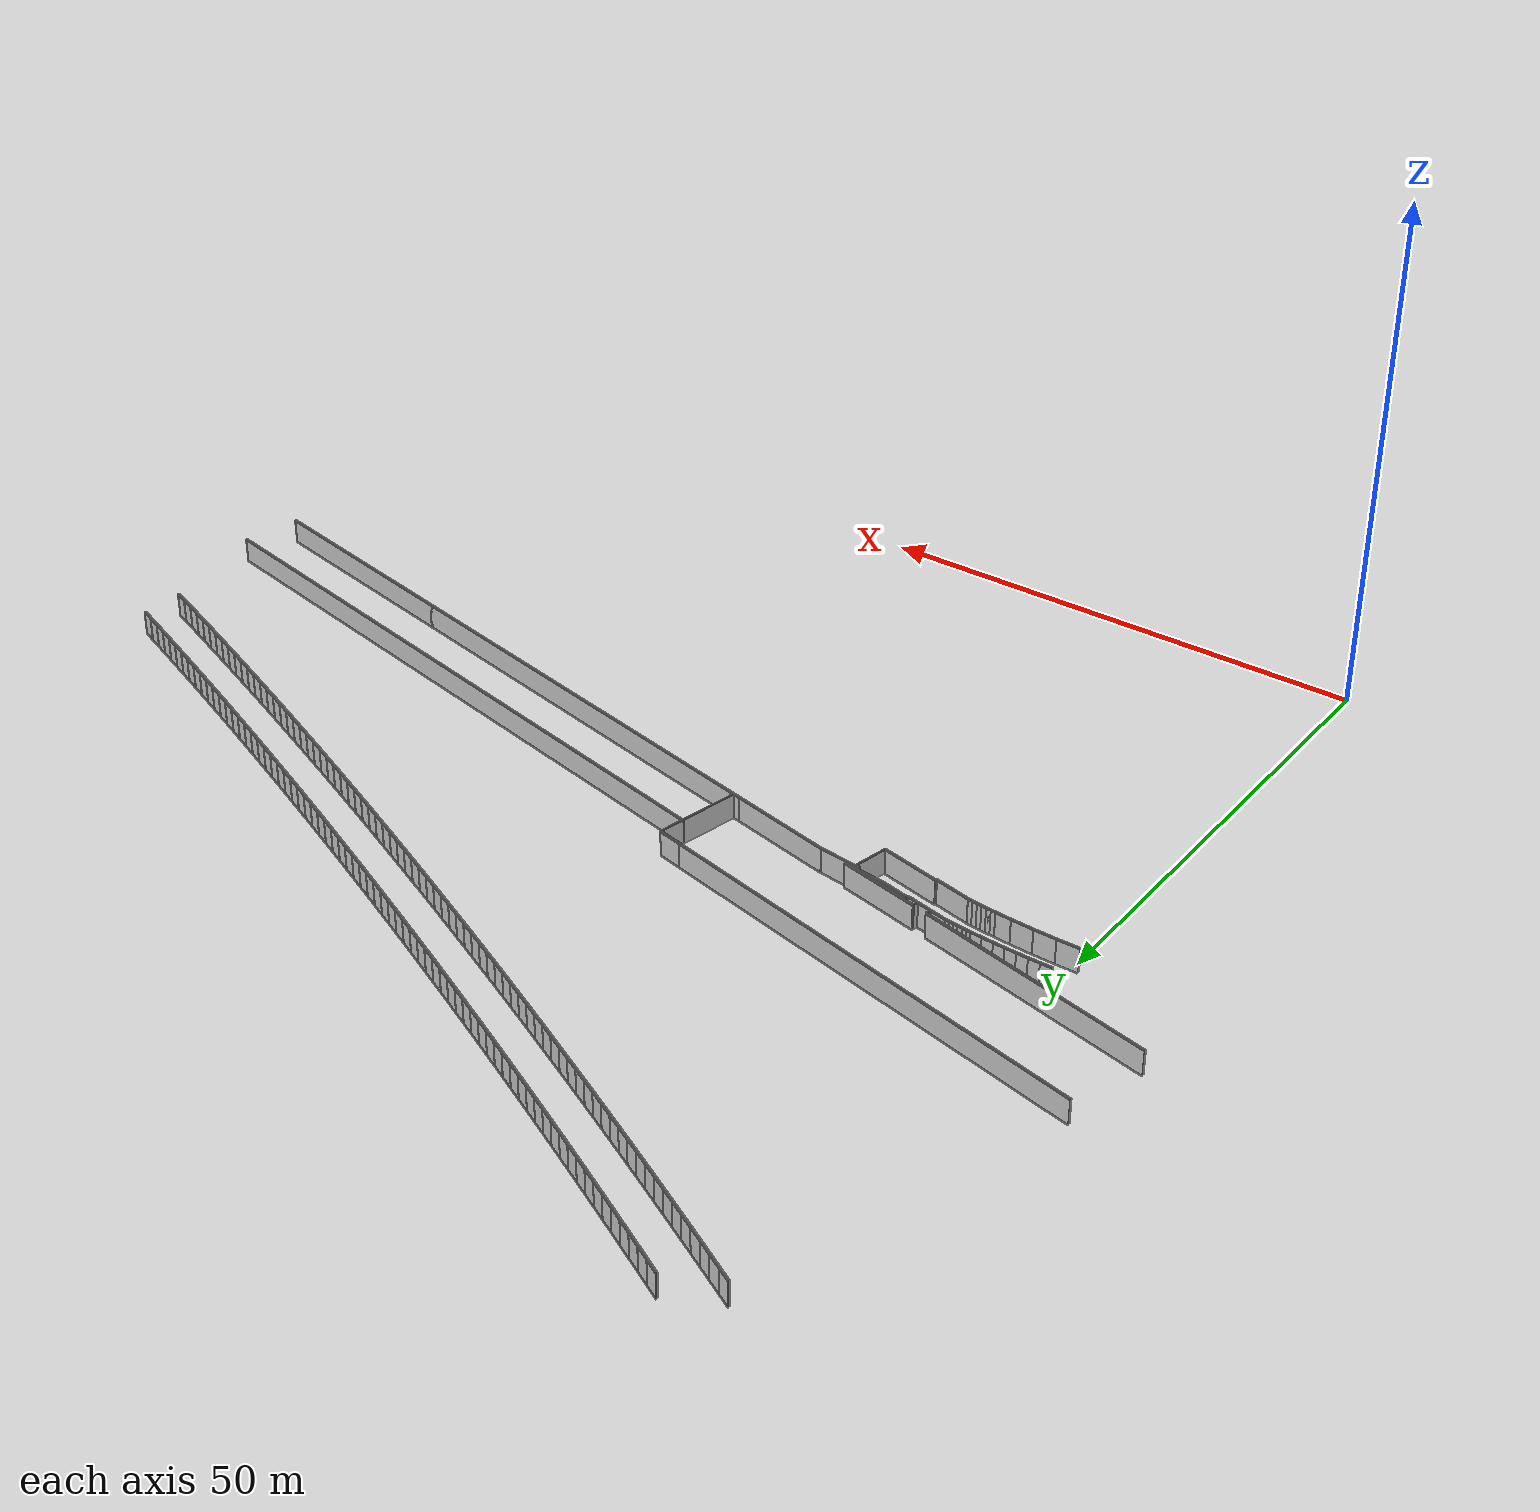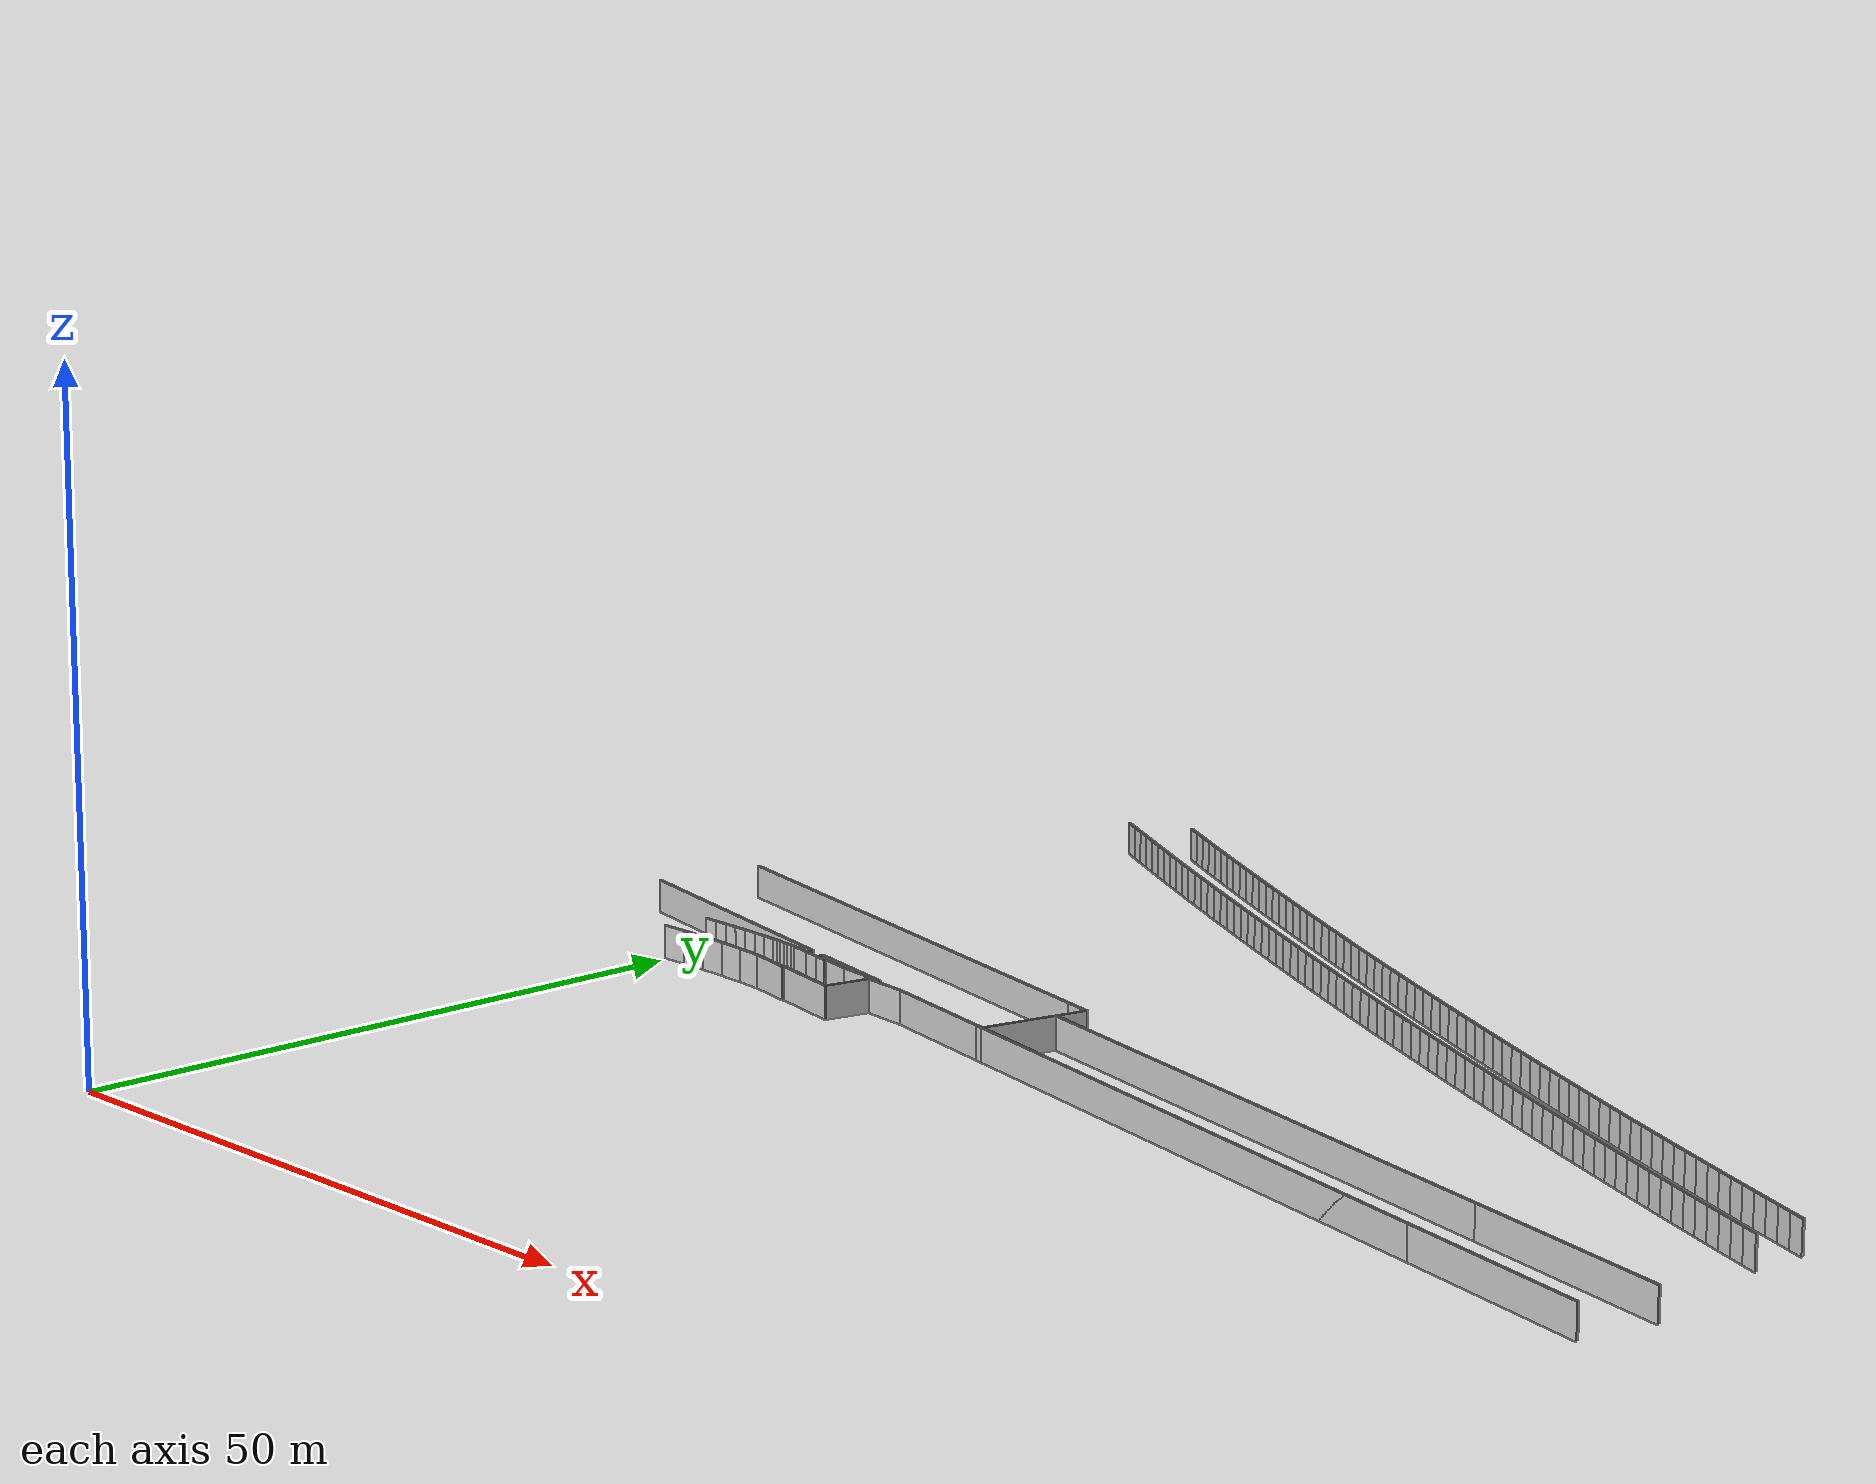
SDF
<?xml version="1.0" ?>
<sdf version="1.6">
  <model name="sps_0702">
    <pose frame="">0 0 0 0 -0 0</pose>
    <static>1</static>
    <self_collide>0</self_collide>
    <allow_auto_disable>0</allow_auto_disable>
    <link name="Wall19">
      <kinematic>0</kinematic>
      <gravity>1</gravity>
      <self_collide>0</self_collide>
      <collision name="collision">
        <geometry>
          <box>
            <size>0.558052 0.15 2.5</size>
          </box>
        </geometry>
        <pose frame="">0 0 0 0 -0 0</pose>
      </collision>
      <visual name="visual">
        <geometry>
          <box>
            <size>0.558052 0.15 2.5</size>
          </box>
        </geometry>
        <pose frame="">0 0 0 0 -0 0</pose>
        <cast_shadows>1</cast_shadows>
        <transparency>0.0</transparency>
      </visual>
      <pose frame="">13.4909 53.7197 1.25 0 -0 1.37308</pose>
    </link>
    <link name="Wall20">
      <kinematic>0</kinematic>
      <gravity>1</gravity>
      <self_collide>0</self_collide>
      <collision name="collision">
        <geometry>
          <box>
            <size>2.70593 0.15 2.5</size>
          </box>
        </geometry>
        <pose frame="">0 0 0 0 -0 0</pose>
      </collision>
      <visual name="visual">
        <geometry>
          <box>
            <size>2.70593 0.15 2.5</size>
          </box>
        </geometry>
        <pose frame="">0 0 0 0 -0 0</pose>
        <cast_shadows>1</cast_shadows>
        <transparency>0.0</transparency>
      </visual>
      <pose frame="">15.9428 53.0665 1.25 0 -0 2.94384</pose>
    </link>
    <link name="Wall21">
      <kinematic>0</kinematic>
      <gravity>1</gravity>
      <self_collide>0</self_collide>
      <collision name="collision">
        <geometry>
          <box>
            <size>0.432153 0.15 2.5</size>
          </box>
        </geometry>
        <pose frame="">0 0 0 0 -0 0</pose>
      </collision>
      <visual name="visual">
        <geometry>
          <box>
            <size>0.432153 0.15 2.5</size>
          </box>
        </geometry>
        <pose frame="">0 0 0 0 -0 0</pose>
        <cast_shadows>1</cast_shadows>
        <transparency>0.0</transparency>
      </visual>
      <pose frame="">20.2974 52.1939 1.25 0 0 -0.199473</pose>
    </link>
    <link name="Wall22">
      <kinematic>0</kinematic>
      <gravity>1</gravity>
      <self_collide>0</self_collide>
      <collision name="collision">
        <geometry>
          <box>
            <size>2.40359 0.15 2.5</size>
          </box>
        </geometry>
        <pose frame="">0 0 0 0 -0 0</pose>
      </collision>
      <visual name="visual">
        <geometry>
          <box>
            <size>2.40359 0.15 2.5</size>
          </box>
        </geometry>
        <pose frame="">0 0 0 0 -0 0</pose>
        <cast_shadows>1</cast_shadows>
        <transparency>0.0</transparency>
      </visual>
      <pose frame="">35.6465 58.1709 1.25 0 -0 2.9385</pose>
    </link>
    <link name="Wall23">
      <kinematic>0</kinematic>
      <gravity>1</gravity>
      <self_collide>0</self_collide>
      <collision name="collision">
        <geometry>
          <box>
            <size>44.7209 0.15 2.5</size>
          </box>
        </geometry>
        <pose frame="">0 0 0 0 -0 0</pose>
      </collision>
      <visual name="visual">
        <geometry>
          <box>
            <size>44.7209 0.15 2.5</size>
          </box>
        </geometry>
        <pose frame="">0 0 0 0 -0 0</pose>
        <cast_shadows>1</cast_shadows>
        <transparency>0.0</transparency>
      </visual>
      <pose frame="">12.5686 62.9235 1.25 0 -0 2.9385</pose>
    </link>
    <link name="Wall24">
      <kinematic>0</kinematic>
      <gravity>1</gravity>
      <self_collide>0</self_collide>
      <collision name="collision">
        <geometry>
          <box>
            <size>17.1475 0.15 2.5</size>
          </box>
        </geometry>
        <pose frame="">0 0 0 0 -0 0</pose>
      </collision>
      <visual name="visual">
        <geometry>
          <box>
            <size>17.1475 0.15 2.5</size>
          </box>
        </geometry>
        <pose frame="">0 0 0 0 -0 0</pose>
        <cast_shadows>1</cast_shadows>
        <transparency>0.0</transparency>
      </visual>
      <pose frame="">92.8679 37.7551 1.25 0 -0 2.93901</pose>
    </link>
    <link name="Wall25">
      <kinematic>0</kinematic>
      <gravity>1</gravity>
      <self_collide>0</self_collide>
      <collision name="collision">
        <geometry>
          <box>
            <size>51.0438 0.15 2.5</size>
          </box>
        </geometry>
        <pose frame="">0 0 0 0 -0 0</pose>
      </collision>
      <visual name="visual">
        <geometry>
          <box>
            <size>51.0438 0.15 2.5</size>
          </box>
        </geometry>
        <pose frame="">0 0 0 0 -0 0</pose>
        <cast_shadows>1</cast_shadows>
        <transparency>0.0</transparency>
      </visual>
      <pose frame="">59.4694 44.6151 1.25 0 -0 2.93901</pose>
    </link>
    <link name="Wall26">
      <kinematic>0</kinematic>
      <gravity>1</gravity>
      <self_collide>0</self_collide>
      <collision name="collision">
        <geometry>
          <box>
            <size>10.4229 0.15 2.5</size>
          </box>
        </geometry>
        <pose frame="">0 0 0 0 -0 0</pose>
      </collision>
      <visual name="visual">
        <geometry>
          <box>
            <size>10.4229 0.15 2.5</size>
          </box>
        </geometry>
        <pose frame="">0 0 0 0 -0 0</pose>
        <cast_shadows>1</cast_shadows>
        <transparency>0.0</transparency>
      </visual>
      <pose frame="">29.3646 50.7986 1.25 0 -0 2.93901</pose>
    </link>
    <link name="Wall112">
      <kinematic>0</kinematic>
      <gravity>1</gravity>
      <self_collide>0</self_collide>
      <collision name="collision">
        <geometry>
          <box>
            <size>23.6286 0.15 2.5</size>
          </box>
        </geometry>
        <pose frame="">0 0 0 0 -0 0</pose>
      </collision>
      <visual name="visual">
        <geometry>
          <box>
            <size>23.6286 0.15 2.5</size>
          </box>
        </geometry>
        <pose frame="">0 0 0 0 -0 0</pose>
        <cast_shadows>1</cast_shadows>
        <transparency>0.0</transparency>
      </visual>
      <pose frame="">0.518974 56.6976 1.25 0 -0 2.93608</pose>
    </link>
    <link name="Wall113">
      <kinematic>0</kinematic>
      <gravity>1</gravity>
      <self_collide>0</self_collide>
      <collision name="collision">
        <geometry>
          <box>
            <size>1.18026 0.15 2.5</size>
          </box>
        </geometry>
        <pose frame="">0 0 0 0 -0 0</pose>
      </collision>
      <visual name="visual">
        <geometry>
          <box>
            <size>1.18026 0.15 2.5</size>
          </box>
        </geometry>
        <pose frame="">0 0 0 0 -0 0</pose>
        <cast_shadows>1</cast_shadows>
        <transparency>0.0</transparency>
      </visual>
      <pose frame="">14.0147 53.3301 1.25 0 -0 2.94369</pose>
    </link>
    <link name="Wall114">
      <kinematic>0</kinematic>
      <gravity>1</gravity>
      <self_collide>0</self_collide>
      <collision name="collision">
        <geometry>
          <box>
            <size>4.19215 0.15 2.5</size>
          </box>
        </geometry>
        <pose frame="">0 0 0 0 -0 0</pose>
      </collision>
      <visual name="visual">
        <geometry>
          <box>
            <size>4.19215 0.15 2.5</size>
          </box>
        </geometry>
        <pose frame="">0 0 0 0 -0 0</pose>
        <cast_shadows>1</cast_shadows>
        <transparency>0.0</transparency>
      </visual>
      <pose frame="">22.1727 52.0419 1.25 0 -0 3.04853</pose>
    </link>
    <link name="Wall280">
      <kinematic>0</kinematic>
      <gravity>1</gravity>
      <self_collide>0</self_collide>
      <collision name="collision">
        <geometry>
          <box>
            <size>0.558807 0.15 2.5</size>
          </box>
        </geometry>
        <pose frame="">0 0 0 0 -0 0</pose>
      </collision>
      <visual name="visual">
        <geometry>
          <box>
            <size>0.558807 0.15 2.5</size>
          </box>
        </geometry>
        <pose frame="">0 0 0 0 -0 0</pose>
        <cast_shadows>1</cast_shadows>
        <transparency>0.0</transparency>
      </visual>
      <pose frame="">12.0295 54.0128 1.25 0 -0 1.3719</pose>
    </link>
    <link name="Wall349">
      <kinematic>0</kinematic>
      <gravity>1</gravity>
      <self_collide>0</self_collide>
      <collision name="collision">
        <geometry>
          <box>
            <size>3.64209 0.15 2.5</size>
          </box>
        </geometry>
        <pose frame="">0 0 0 0 -0 0</pose>
      </collision>
      <visual name="visual">
        <geometry>
          <box>
            <size>3.64209 0.15 2.5</size>
          </box>
        </geometry>
        <pose frame="">0 0 0 0 -0 0</pose>
        <cast_shadows>1</cast_shadows>
        <transparency>0.0</transparency>
      </visual>
      <pose frame="">12.1271 50.1795 1.25 0 -0 2.93845</pose>
    </link>
    <link name="Wall350">
      <kinematic>0</kinematic>
      <gravity>1</gravity>
      <self_collide>0</self_collide>
      <collision name="collision">
        <geometry>
          <box>
            <size>0.12085 0.15 2.5</size>
          </box>
        </geometry>
        <pose frame="">0 0 0 0 -0 0</pose>
      </collision>
      <visual name="visual">
        <geometry>
          <box>
            <size>0.12085 0.15 2.5</size>
          </box>
        </geometry>
        <pose frame="">0 0 0 0 -0 0</pose>
        <cast_shadows>1</cast_shadows>
        <transparency>0.0</transparency>
      </visual>
      <pose frame="">13.9228 49.8713 1.25 0 0 -1.77215</pose>
    </link>
    <link name="Wall429">
      <kinematic>0</kinematic>
      <gravity>1</gravity>
      <self_collide>0</self_collide>
      <collision name="collision">
        <geometry>
          <box>
            <size>1.63883 0.15 2.5</size>
          </box>
        </geometry>
        <pose frame="">0 0 0 0 -0 0</pose>
      </collision>
      <visual name="visual">
        <geometry>
          <box>
            <size>1.63883 0.15 2.5</size>
          </box>
        </geometry>
        <pose frame="">0 0 0 0 -0 0</pose>
        <cast_shadows>1</cast_shadows>
        <transparency>0.0</transparency>
      </visual>
      <pose frame="">11.1709 53.9001 1.25 0 0 -0.198009</pose>
    </link>
    <link name="Wall430">
      <kinematic>0</kinematic>
      <gravity>1</gravity>
      <self_collide>0</self_collide>
      <collision name="collision">
        <geometry>
          <box>
            <size>4.19215 0.15 2.5</size>
          </box>
        </geometry>
        <pose frame="">0 0 0 0 -0 0</pose>
      </collision>
      <visual name="visual">
        <geometry>
          <box>
            <size>4.19215 0.15 2.5</size>
          </box>
        </geometry>
        <pose frame="">0 0 0 0 -0 0</pose>
        <cast_shadows>1</cast_shadows>
        <transparency>0.0</transparency>
      </visual>
      <pose frame="">19.3564 52.6059 1.25 0 -0 3.04853</pose>
    </link>
    <link name="Wall431">
      <kinematic>0</kinematic>
      <gravity>1</gravity>
      <self_collide>0</self_collide>
      <collision name="collision">
        <geometry>
          <box>
            <size>8.0547 0.15 2.5</size>
          </box>
        </geometry>
        <pose frame="">0 0 0 0 -0 0</pose>
      </collision>
      <visual name="visual">
        <geometry>
          <box>
            <size>8.0547 0.15 2.5</size>
          </box>
        </geometry>
        <pose frame="">0 0 0 0 -0 0</pose>
        <cast_shadows>1</cast_shadows>
        <transparency>0.0</transparency>
      </visual>
      <pose frame="">17.4946 53.2022 1.25 0 -0 2.94387</pose>
    </link>
    <link name="Wall524">
      <kinematic>0</kinematic>
      <gravity>1</gravity>
      <self_collide>0</self_collide>
      <collision name="collision">
        <geometry>
          <box>
            <size>3.50128 0.15 2.5</size>
          </box>
        </geometry>
        <pose frame="">0 0 0 0 -0 0</pose>
      </collision>
      <visual name="visual">
        <geometry>
          <box>
            <size>3.50128 0.15 2.5</size>
          </box>
        </geometry>
        <pose frame="">0 0 0 0 -0 0</pose>
        <cast_shadows>1</cast_shadows>
        <transparency>0.0</transparency>
      </visual>
      <pose frame="">20.1558 50.4365 1.25 0 0 -1.77406</pose>
    </link>
    <link name="Wall525">
      <kinematic>0</kinematic>
      <gravity>1</gravity>
      <self_collide>0</self_collide>
      <collision name="collision">
        <geometry>
          <box>
            <size>2.50024 0.15 2.5</size>
          </box>
        </geometry>
        <pose frame="">0 0 0 0 -0 0</pose>
      </collision>
      <visual name="visual">
        <geometry>
          <box>
            <size>2.50024 0.15 2.5</size>
          </box>
        </geometry>
        <pose frame="">0 0 0 0 -0 0</pose>
        <cast_shadows>1</cast_shadows>
        <transparency>0.0</transparency>
      </visual>
      <pose frame="">36.5713 56.7041 1.25 0 -0 1.36759</pose>
    </link>
    <link name="Wall607">
      <kinematic>0</kinematic>
      <gravity>1</gravity>
      <self_collide>0</self_collide>
      <collision name="collision">
        <geometry>
          <box>
            <size>0.120432 0.15 2.5</size>
          </box>
        </geometry>
        <pose frame="">0 0 0 0 -0 0</pose>
      </collision>
      <visual name="visual">
        <geometry>
          <box>
            <size>0.120432 0.15 2.5</size>
          </box>
        </geometry>
        <pose frame="">0 0 0 0 -0 0</pose>
        <cast_shadows>1</cast_shadows>
        <transparency>0.0</transparency>
      </visual>
      <pose frame="">14.6048 53.2732 1.25 0 0 -1.76253</pose>
    </link>
    <link name="Wall609">
      <kinematic>0</kinematic>
      <gravity>1</gravity>
      <self_collide>0</self_collide>
      <collision name="collision">
        <geometry>
          <box>
            <size>18.3831 0.15 2.5</size>
          </box>
        </geometry>
        <pose frame="">0 0 0 0 -0 0</pose>
      </collision>
      <visual name="visual">
        <geometry>
          <box>
            <size>18.3831 0.15 2.5</size>
          </box>
        </geometry>
        <pose frame="">0 0 0 0 -0 0</pose>
        <cast_shadows>1</cast_shadows>
        <transparency>0.0</transparency>
      </visual>
      <pose frame="">93.4734 43.7539 1.25 0 -0 2.93924</pose>
    </link>
    <link name="Wall610">
      <kinematic>0</kinematic>
      <gravity>1</gravity>
      <self_collide>0</self_collide>
      <collision name="collision">
        <geometry>
          <box>
            <size>49.1533 0.15 2.5</size>
          </box>
        </geometry>
        <pose frame="">0 0 0 0 -0 0</pose>
      </collision>
      <visual name="visual">
        <geometry>
          <box>
            <size>49.1533 0.15 2.5</size>
          </box>
        </geometry>
        <pose frame="">0 0 0 0 -0 0</pose>
        <cast_shadows>1</cast_shadows>
        <transparency>0.0</transparency>
      </visual>
      <pose frame="">60.3942 50.5404 1.25 0 -0 2.93924</pose>
    </link>
    <link name="Wall1000">
      <kinematic>0</kinematic>
      <gravity>1</gravity>
      <self_collide>0</self_collide>
      <collision name="collision">
        <geometry>
          <box>
            <size>67.5356 0.15 2.5</size>
          </box>
        </geometry>
        <pose frame="">0 0 0 0 -0 0</pose>
      </collision>
      <visual name="visual">
        <geometry>
          <box>
            <size>67.5356 0.15 2.5</size>
          </box>
        </geometry>
        <pose frame="">0 0 0 0 -0 0</pose>
        <cast_shadows>1</cast_shadows>
        <transparency>0.0</transparency>
      </visual>
      <pose frame="">68.189 42.824 1.25 0 -0 2.93902</pose>
    </link>
    <link name="Wall1001">
      <kinematic>0</kinematic>
      <gravity>1</gravity>
      <self_collide>0</self_collide>
      <collision name="collision">
        <geometry>
          <box>
            <size>5.98487 0.15 2.5</size>
          </box>
        </geometry>
        <pose frame="">0 0 0 0 -0 0</pose>
      </collision>
      <visual name="visual">
        <geometry>
          <box>
            <size>5.98487 0.15 2.5</size>
          </box>
        </geometry>
        <pose frame="">0 0 0 0 -0 0</pose>
        <cast_shadows>1</cast_shadows>
        <transparency>0.0</transparency>
      </visual>
      <pose frame="">35.7154 52.5488 1.25 0 -0 1.36766</pose>
    </link>
    <link name="Wall1002">
      <kinematic>0</kinematic>
      <gravity>1</gravity>
      <self_collide>0</self_collide>
      <collision name="collision">
        <geometry>
          <box>
            <size>67.5363 0.15 2.5</size>
          </box>
        </geometry>
        <pose frame="">0 0 0 0 -0 0</pose>
      </collision>
      <visual name="visual">
        <geometry>
          <box>
            <size>67.5363 0.15 2.5</size>
          </box>
        </geometry>
        <pose frame="">0 0 0 0 -0 0</pose>
        <cast_shadows>1</cast_shadows>
        <transparency>0.0</transparency>
      </visual>
      <pose frame="">69.3982 48.6932 1.25 0 0 -0.202351</pose>
    </link>
    <link name="Wall1723">
      <kinematic>0</kinematic>
      <gravity>1</gravity>
      <self_collide>0</self_collide>
      <collision name="collision">
        <geometry>
          <box>
            <size>1.1106 0.15 2.5</size>
          </box>
        </geometry>
        <pose frame="">0 0 0 0 -0 0</pose>
      </collision>
      <visual name="visual">
        <geometry>
          <box>
            <size>1.1106 0.15 2.5</size>
          </box>
        </geometry>
        <pose frame="">0 0 0 0 -0 0</pose>
        <cast_shadows>1</cast_shadows>
        <transparency>0.0</transparency>
      </visual>
      <pose frame="">0.546867 54.4314 1.25 0 -0 0.0181918</pose>
    </link>
    <link name="Wall1724">
      <kinematic>0</kinematic>
      <gravity>1</gravity>
      <self_collide>0</self_collide>
      <collision name="collision">
        <geometry>
          <box>
            <size>1.11043 0.15 2.5</size>
          </box>
        </geometry>
        <pose frame="">0 0 0 0 -0 0</pose>
      </collision>
      <visual name="visual">
        <geometry>
          <box>
            <size>1.11043 0.15 2.5</size>
          </box>
        </geometry>
        <pose frame="">0 0 0 0 -0 0</pose>
        <cast_shadows>1</cast_shadows>
        <transparency>0.0</transparency>
      </visual>
      <pose frame="">1.65728 54.4446 1.25 0 -0 0.00560649</pose>
    </link>
    <link name="Wall1725">
      <kinematic>0</kinematic>
      <gravity>1</gravity>
      <self_collide>0</self_collide>
      <collision name="collision">
        <geometry>
          <box>
            <size>1.11038 0.15 2.5</size>
          </box>
        </geometry>
        <pose frame="">0 0 0 0 -0 0</pose>
      </collision>
      <visual name="visual">
        <geometry>
          <box>
            <size>1.11038 0.15 2.5</size>
          </box>
        </geometry>
        <pose frame="">0 0 0 0 -0 0</pose>
        <cast_shadows>1</cast_shadows>
        <transparency>0.0</transparency>
      </visual>
      <pose frame="">2.76766 54.4436 1.25 0 0 -0.00742071</pose>
    </link>
    <link name="Wall1726">
      <kinematic>0</kinematic>
      <gravity>1</gravity>
      <self_collide>0</self_collide>
      <collision name="collision">
        <geometry>
          <box>
            <size>1.11063 0.15 2.5</size>
          </box>
        </geometry>
        <pose frame="">0 0 0 0 -0 0</pose>
      </collision>
      <visual name="visual">
        <geometry>
          <box>
            <size>1.11063 0.15 2.5</size>
          </box>
        </geometry>
        <pose frame="">0 0 0 0 -0 0</pose>
        <cast_shadows>1</cast_shadows>
        <transparency>0.0</transparency>
      </visual>
      <pose frame="">3.87804 54.4285 1.25 0 0 -0.0197852</pose>
    </link>
    <link name="Wall1727">
      <kinematic>0</kinematic>
      <gravity>1</gravity>
      <self_collide>0</self_collide>
      <collision name="collision">
        <geometry>
          <box>
            <size>1.11039 0.15 2.5</size>
          </box>
        </geometry>
        <pose frame="">0 0 0 0 -0 0</pose>
      </collision>
      <visual name="visual">
        <geometry>
          <box>
            <size>1.11039 0.15 2.5</size>
          </box>
        </geometry>
        <pose frame="">0 0 0 0 -0 0</pose>
        <cast_shadows>1</cast_shadows>
        <transparency>0.0</transparency>
      </visual>
      <pose frame="">4.98815 54.3994 1.25 0 0 -0.0326013</pose>
    </link>
    <link name="Wall1728">
      <kinematic>0</kinematic>
      <gravity>1</gravity>
      <self_collide>0</self_collide>
      <collision name="collision">
        <geometry>
          <box>
            <size>1.11033 0.15 2.5</size>
          </box>
        </geometry>
        <pose frame="">0 0 0 0 -0 0</pose>
      </collision>
      <visual name="visual">
        <geometry>
          <box>
            <size>1.11033 0.15 2.5</size>
          </box>
        </geometry>
        <pose frame="">0 0 0 0 -0 0</pose>
        <cast_shadows>1</cast_shadows>
        <transparency>0.0</transparency>
      </visual>
      <pose frame="">6.09765 54.3562 1.25 0 0 -0.045256</pose>
    </link>
    <link name="Wall1729">
      <kinematic>0</kinematic>
      <gravity>1</gravity>
      <self_collide>0</self_collide>
      <collision name="collision">
        <geometry>
          <box>
            <size>1.11041 0.15 2.5</size>
          </box>
        </geometry>
        <pose frame="">0 0 0 0 -0 0</pose>
      </collision>
      <visual name="visual">
        <geometry>
          <box>
            <size>1.11041 0.15 2.5</size>
          </box>
        </geometry>
        <pose frame="">0 0 0 0 -0 0</pose>
        <cast_shadows>1</cast_shadows>
        <transparency>0.0</transparency>
      </visual>
      <pose frame="">7.20653 54.2992 1.25 0 0 -0.0574712</pose>
    </link>
    <link name="Wall1730">
      <kinematic>0</kinematic>
      <gravity>1</gravity>
      <self_collide>0</self_collide>
      <collision name="collision">
        <geometry>
          <box>
            <size>0.436024 0.15 2.5</size>
          </box>
        </geometry>
        <pose frame="">0 0 0 0 -0 0</pose>
      </collision>
      <visual name="visual">
        <geometry>
          <box>
            <size>0.436024 0.15 2.5</size>
          </box>
        </geometry>
        <pose frame="">0 0 0 0 -0 0</pose>
        <cast_shadows>1</cast_shadows>
        <transparency>0.0</transparency>
      </visual>
      <pose frame="">7.97835 54.2528 1.25 0 0 -0.0665402</pose>
    </link>
    <link name="Wall1731">
      <kinematic>0</kinematic>
      <gravity>1</gravity>
      <self_collide>0</self_collide>
      <collision name="collision">
        <geometry>
          <box>
            <size>0.435871 0.15 2.5</size>
          </box>
        </geometry>
        <pose frame="">0 0 0 0 -0 0</pose>
      </collision>
      <visual name="visual">
        <geometry>
          <box>
            <size>0.435871 0.15 2.5</size>
          </box>
        </geometry>
        <pose frame="">0 0 0 0 -0 0</pose>
        <cast_shadows>1</cast_shadows>
        <transparency>0.0</transparency>
      </visual>
      <pose frame="">8.41326 54.2227 1.25 0 0 -0.0716167</pose>
    </link>
    <link name="Wall1732">
      <kinematic>0</kinematic>
      <gravity>1</gravity>
      <self_collide>0</self_collide>
      <collision name="collision">
        <geometry>
          <box>
            <size>0.435715 0.15 2.5</size>
          </box>
        </geometry>
        <pose frame="">0 0 0 0 -0 0</pose>
      </collision>
      <visual name="visual">
        <geometry>
          <box>
            <size>0.435715 0.15 2.5</size>
          </box>
        </geometry>
        <pose frame="">0 0 0 0 -0 0</pose>
        <cast_shadows>1</cast_shadows>
        <transparency>0.0</transparency>
      </visual>
      <pose frame="">8.84786 54.1905 1.25 0 0 -0.0762777</pose>
    </link>
    <link name="Wall1733">
      <kinematic>0</kinematic>
      <gravity>1</gravity>
      <self_collide>0</self_collide>
      <collision name="collision">
        <geometry>
          <box>
            <size>0.435827 0.15 2.5</size>
          </box>
        </geometry>
        <pose frame="">0 0 0 0 -0 0</pose>
      </collision>
      <visual name="visual">
        <geometry>
          <box>
            <size>0.435827 0.15 2.5</size>
          </box>
        </geometry>
        <pose frame="">0 0 0 0 -0 0</pose>
        <cast_shadows>1</cast_shadows>
        <transparency>0.0</transparency>
      </visual>
      <pose frame="">9.28228 54.1562 1.25 0 0 -0.0813153</pose>
    </link>
    <link name="Wall1734">
      <kinematic>0</kinematic>
      <gravity>1</gravity>
      <self_collide>0</self_collide>
      <collision name="collision">
        <geometry>
          <box>
            <size>0.435813 0.15 2.5</size>
          </box>
        </geometry>
        <pose frame="">0 0 0 0 -0 0</pose>
      </collision>
      <visual name="visual">
        <geometry>
          <box>
            <size>0.435813 0.15 2.5</size>
          </box>
        </geometry>
        <pose frame="">0 0 0 0 -0 0</pose>
        <cast_shadows>1</cast_shadows>
        <transparency>0.0</transparency>
      </visual>
      <pose frame="">9.71657 54.1198 1.25 0 0 -0.0859558</pose>
    </link>
    <link name="Wall1735">
      <kinematic>0</kinematic>
      <gravity>1</gravity>
      <self_collide>0</self_collide>
      <collision name="collision">
        <geometry>
          <box>
            <size>0.435781 0.15 2.5</size>
          </box>
        </geometry>
        <pose frame="">0 0 0 0 -0 0</pose>
      </collision>
      <visual name="visual">
        <geometry>
          <box>
            <size>0.435781 0.15 2.5</size>
          </box>
        </geometry>
        <pose frame="">0 0 0 0 -0 0</pose>
        <cast_shadows>1</cast_shadows>
        <transparency>0.0</transparency>
      </visual>
      <pose frame="">10.1507 54.0812 1.25 0 0 -0.0914461</pose>
    </link>
    <link name="Wall1736">
      <kinematic>0</kinematic>
      <gravity>1</gravity>
      <self_collide>0</self_collide>
      <collision name="collision">
        <geometry>
          <box>
            <size>1.63901 0.15 2.5</size>
          </box>
        </geometry>
        <pose frame="">0 0 0 0 -0 0</pose>
      </collision>
      <visual name="visual">
        <geometry>
          <box>
            <size>1.63901 0.15 2.5</size>
          </box>
        </geometry>
        <pose frame="">0 0 0 0 -0 0</pose>
        <cast_shadows>1</cast_shadows>
        <transparency>0.0</transparency>
      </visual>
      <pose frame="">11.1711 53.9001 1.25 0 0 -0.197987</pose>
    </link>
    <link name="Wall1737">
      <kinematic>0</kinematic>
      <gravity>1</gravity>
      <self_collide>0</self_collide>
      <collision name="collision">
        <geometry>
          <box>
            <size>1.49061 0.15 2.5</size>
          </box>
        </geometry>
        <pose frame="">0 0 0 0 -0 0</pose>
      </collision>
      <visual name="visual">
        <geometry>
          <box>
            <size>1.49061 0.15 2.5</size>
          </box>
        </geometry>
        <pose frame="">0 0 0 0 -0 0</pose>
        <cast_shadows>1</cast_shadows>
        <transparency>0.0</transparency>
      </visual>
      <pose frame="">12.7054 53.5926 1.25 0 0 -0.19758</pose>
    </link>
    <link name="Wall1738">
      <kinematic>0</kinematic>
      <gravity>1</gravity>
      <self_collide>0</self_collide>
      <collision name="collision">
        <geometry>
          <box>
            <size>1.1803 0.15 2.5</size>
          </box>
        </geometry>
        <pose frame="">0 0 0 0 -0 0</pose>
      </collision>
      <visual name="visual">
        <geometry>
          <box>
            <size>1.1803 0.15 2.5</size>
          </box>
        </geometry>
        <pose frame="">0 0 0 0 -0 0</pose>
        <cast_shadows>1</cast_shadows>
        <transparency>0.0</transparency>
      </visual>
      <pose frame="">14.0149 53.3302 1.25 0 0 -0.198055</pose>
    </link>
    <link name="Wall1739">
      <kinematic>0</kinematic>
      <gravity>1</gravity>
      <self_collide>0</self_collide>
      <collision name="collision">
        <geometry>
          <box>
            <size>0.120623 0.15 2.5</size>
          </box>
        </geometry>
        <pose frame="">0 0 0 0 -0 0</pose>
      </collision>
      <visual name="visual">
        <geometry>
          <box>
            <size>0.120623 0.15 2.5</size>
          </box>
        </geometry>
        <pose frame="">0 0 0 0 -0 0</pose>
        <cast_shadows>1</cast_shadows>
        <transparency>0.0</transparency>
      </visual>
      <pose frame="">14.605 53.2733 1.25 0 -0 1.37886</pose>
    </link>
    <link name="Wall1740">
      <kinematic>0</kinematic>
      <gravity>1</gravity>
      <self_collide>0</self_collide>
      <collision name="collision">
        <geometry>
          <box>
            <size>2.70597 0.15 2.5</size>
          </box>
        </geometry>
        <pose frame="">0 0 0 0 -0 0</pose>
      </collision>
      <visual name="visual">
        <geometry>
          <box>
            <size>2.70597 0.15 2.5</size>
          </box>
        </geometry>
        <pose frame="">0 0 0 0 -0 0</pose>
        <cast_shadows>1</cast_shadows>
        <transparency>0.0</transparency>
      </visual>
      <pose frame="">15.9431 53.0666 1.25 0 0 -0.197816</pose>
    </link>
    <link name="Wall1741">
      <kinematic>0</kinematic>
      <gravity>1</gravity>
      <self_collide>0</self_collide>
      <collision name="collision">
        <geometry>
          <box>
            <size>2.85635 0.15 2.5</size>
          </box>
        </geometry>
        <pose frame="">0 0 0 0 -0 0</pose>
      </collision>
      <visual name="visual">
        <geometry>
          <box>
            <size>2.85635 0.15 2.5</size>
          </box>
        </geometry>
        <pose frame="">0 0 0 0 -0 0</pose>
        <cast_shadows>1</cast_shadows>
        <transparency>0.0</transparency>
      </visual>
      <pose frame="">18.6917 52.668 1.25 0 0 -0.0930433</pose>
    </link>
    <link name="Wall1742">
      <kinematic>0</kinematic>
      <gravity>1</gravity>
      <self_collide>0</self_collide>
      <collision name="collision">
        <geometry>
          <box>
            <size>0.299878 0.15 2.5</size>
          </box>
        </geometry>
        <pose frame="">0 0 0 0 -0 0</pose>
      </collision>
      <visual name="visual">
        <geometry>
          <box>
            <size>0.299878 0.15 2.5</size>
          </box>
        </geometry>
        <pose frame="">0 0 0 0 -0 0</pose>
        <cast_shadows>1</cast_shadows>
        <transparency>0.0</transparency>
      </visual>
      <pose frame="">20.0998 52.386 1.25 0 0 -1.66374</pose>
    </link>
    <link name="Wall1743">
      <kinematic>0</kinematic>
      <gravity>1</gravity>
      <self_collide>0</self_collide>
      <collision name="collision">
        <geometry>
          <box>
            <size>0.432213 0.15 2.5</size>
          </box>
        </geometry>
        <pose frame="">0 0 0 0 -0 0</pose>
      </collision>
      <visual name="visual">
        <geometry>
          <box>
            <size>0.432213 0.15 2.5</size>
          </box>
        </geometry>
        <pose frame="">0 0 0 0 -0 0</pose>
        <cast_shadows>1</cast_shadows>
        <transparency>0.0</transparency>
      </visual>
      <pose frame="">20.2977 52.1939 1.25 0 0 -0.199445</pose>
    </link>
    <link name="Wall1744">
      <kinematic>0</kinematic>
      <gravity>1</gravity>
      <self_collide>0</self_collide>
      <collision name="collision">
        <geometry>
          <box>
            <size>3.50124 0.15 2.5</size>
          </box>
        </geometry>
        <pose frame="">0 0 0 0 -0 0</pose>
      </collision>
      <visual name="visual">
        <geometry>
          <box>
            <size>3.50124 0.15 2.5</size>
          </box>
        </geometry>
        <pose frame="">0 0 0 0 -0 0</pose>
        <cast_shadows>1</cast_shadows>
        <transparency>0.0</transparency>
      </visual>
      <pose frame="">20.1562 50.4365 1.25 0 0 -1.77401</pose>
    </link>
    <link name="Wall1745">
      <kinematic>0</kinematic>
      <gravity>1</gravity>
      <self_collide>0</self_collide>
      <collision name="collision">
        <geometry>
          <box>
            <size>5.9908 0.15 2.5</size>
          </box>
        </geometry>
        <pose frame="">0 0 0 0 -0 0</pose>
      </collision>
      <visual name="visual">
        <geometry>
          <box>
            <size>5.9908 0.15 2.5</size>
          </box>
        </geometry>
        <pose frame="">0 0 0 0 -0 0</pose>
        <cast_shadows>1</cast_shadows>
        <transparency>0.0</transparency>
      </visual>
      <pose frame="">16.8691 49.3262 1.25 0 -0 2.93845</pose>
    </link>
    <link name="Wall1746">
      <kinematic>0</kinematic>
      <gravity>1</gravity>
      <self_collide>0</self_collide>
      <collision name="collision">
        <geometry>
          <box>
            <size>0.120899 0.15 2.5</size>
          </box>
        </geometry>
        <pose frame="">0 0 0 0 -0 0</pose>
      </collision>
      <visual name="visual">
        <geometry>
          <box>
            <size>0.120899 0.15 2.5</size>
          </box>
        </geometry>
        <pose frame="">0 0 0 0 -0 0</pose>
        <cast_shadows>1</cast_shadows>
        <transparency>0.0</transparency>
      </visual>
      <pose frame="">13.9231 49.8713 1.25 0 0 -1.77413</pose>
    </link>
    <link name="Wall1747">
      <kinematic>0</kinematic>
      <gravity>1</gravity>
      <self_collide>0</self_collide>
      <collision name="collision">
        <geometry>
          <box>
            <size>3.64191 0.15 2.5</size>
          </box>
        </geometry>
        <pose frame="">0 0 0 0 -0 0</pose>
      </collision>
      <visual name="visual">
        <geometry>
          <box>
            <size>3.64191 0.15 2.5</size>
          </box>
        </geometry>
        <pose frame="">0 0 0 0 -0 0</pose>
        <cast_shadows>1</cast_shadows>
        <transparency>0.0</transparency>
      </visual>
      <pose frame="">12.1273 50.1795 1.25 0 -0 2.93844</pose>
    </link>
    <link name="Wall1748">
      <kinematic>0</kinematic>
      <gravity>1</gravity>
      <self_collide>0</self_collide>
      <collision name="collision">
        <geometry>
          <box>
            <size>2.18198 0.15 2.5</size>
          </box>
        </geometry>
        <pose frame="">0 0 0 0 -0 0</pose>
      </collision>
      <visual name="visual">
        <geometry>
          <box>
            <size>2.18198 0.15 2.5</size>
          </box>
        </geometry>
        <pose frame="">0 0 0 0 -0 0</pose>
        <cast_shadows>1</cast_shadows>
        <transparency>0.0</transparency>
      </visual>
      <pose frame="">9.25674 50.639 1.25 0 -0 3.05707</pose>
    </link>
    <link name="Wall1749">
      <kinematic>0</kinematic>
      <gravity>1</gravity>
      <self_collide>0</self_collide>
      <collision name="collision">
        <geometry>
          <box>
            <size>2.18191 0.15 2.5</size>
          </box>
        </geometry>
        <pose frame="">0 0 0 0 -0 0</pose>
      </collision>
      <visual name="visual">
        <geometry>
          <box>
            <size>2.18191 0.15 2.5</size>
          </box>
        </geometry>
        <pose frame="">0 0 0 0 -0 0</pose>
        <cast_shadows>1</cast_shadows>
        <transparency>0.0</transparency>
      </visual>
      <pose frame="">7.08056 50.795 1.25 0 -0 3.08298</pose>
    </link>
    <link name="Wall1750">
      <kinematic>0</kinematic>
      <gravity>1</gravity>
      <self_collide>0</self_collide>
      <collision name="collision">
        <geometry>
          <box>
            <size>2.18202 0.15 2.5</size>
          </box>
        </geometry>
        <pose frame="">0 0 0 0 -0 0</pose>
      </collision>
      <visual name="visual">
        <geometry>
          <box>
            <size>2.18202 0.15 2.5</size>
          </box>
        </geometry>
        <pose frame="">0 0 0 0 -0 0</pose>
        <cast_shadows>1</cast_shadows>
        <transparency>0.0</transparency>
      </visual>
      <pose frame="">4.90105 50.8947 1.25 0 -0 3.10878</pose>
    </link>
    <link name="Wall1751">
      <kinematic>0</kinematic>
      <gravity>1</gravity>
      <self_collide>0</self_collide>
      <collision name="collision">
        <geometry>
          <box>
            <size>2.18182 0.15 2.5</size>
          </box>
        </geometry>
        <pose frame="">0 0 0 0 -0 0</pose>
      </collision>
      <visual name="visual">
        <geometry>
          <box>
            <size>2.18182 0.15 2.5</size>
          </box>
        </geometry>
        <pose frame="">0 0 0 0 -0 0</pose>
        <cast_shadows>1</cast_shadows>
        <transparency>0.0</transparency>
      </visual>
      <pose frame="">2.71975 50.9381 1.25 0 -0 3.13463</pose>
    </link>
    <link name="Wall1752">
      <kinematic>0</kinematic>
      <gravity>1</gravity>
      <self_collide>0</self_collide>
      <collision name="collision">
        <geometry>
          <box>
            <size>2.18203 0.15 2.5</size>
          </box>
        </geometry>
        <pose frame="">0 0 0 0 -0 0</pose>
      </collision>
      <visual name="visual">
        <geometry>
          <box>
            <size>2.18203 0.15 2.5</size>
          </box>
        </geometry>
        <pose frame="">0 0 0 0 -0 0</pose>
        <cast_shadows>1</cast_shadows>
        <transparency>0.0</transparency>
      </visual>
      <pose frame="">0.538047 50.9251 1.25 0 0 -3.12271</pose>
    </link>
    <link name="Wall2728">
      <kinematic>0</kinematic>
      <gravity>1</gravity>
      <self_collide>0</self_collide>
      <collision name="collision">
        <geometry>
          <box>
            <size>0.469425 0.15 2.5</size>
          </box>
        </geometry>
        <pose frame="">0 0 0 0 -0 0</pose>
      </collision>
      <visual name="visual">
        <geometry>
          <box>
            <size>0.469425 0.15 2.5</size>
          </box>
        </geometry>
        <pose frame="">0 0 0 0 -0 0</pose>
        <cast_shadows>1</cast_shadows>
        <transparency>0.0</transparency>
      </visual>
      <pose frame="">7.76986 50.7585 1.25 0 0 -0.0666201</pose>
    </link>
    <link name="Wall2729">
      <kinematic>0</kinematic>
      <gravity>1</gravity>
      <self_collide>0</self_collide>
      <collision name="collision">
        <geometry>
          <box>
            <size>0.469616 0.15 2.5</size>
          </box>
        </geometry>
        <pose frame="">0 0 0 0 -0 0</pose>
      </collision>
      <visual name="visual">
        <geometry>
          <box>
            <size>0.469616 0.15 2.5</size>
          </box>
        </geometry>
        <pose frame="">0 0 0 0 -0 0</pose>
        <cast_shadows>1</cast_shadows>
        <transparency>0.0</transparency>
      </visual>
      <pose frame="">8.23824 50.7259 1.25 0 0 -0.0724557</pose>
    </link>
    <link name="Wall2730">
      <kinematic>0</kinematic>
      <gravity>1</gravity>
      <self_collide>0</self_collide>
      <collision name="collision">
        <geometry>
          <box>
            <size>0.469443 0.15 2.5</size>
          </box>
        </geometry>
        <pose frame="">0 0 0 0 -0 0</pose>
      </collision>
      <visual name="visual">
        <geometry>
          <box>
            <size>0.469443 0.15 2.5</size>
          </box>
        </geometry>
        <pose frame="">0 0 0 0 -0 0</pose>
        <cast_shadows>1</cast_shadows>
        <transparency>0.0</transparency>
      </visual>
      <pose frame="">8.70644 50.6906 1.25 0 0 -0.0779585</pose>
    </link>
    <link name="Wall2731">
      <kinematic>0</kinematic>
      <gravity>1</gravity>
      <self_collide>0</self_collide>
      <collision name="collision">
        <geometry>
          <box>
            <size>0.469417 0.15 2.5</size>
          </box>
        </geometry>
        <pose frame="">0 0 0 0 -0 0</pose>
      </collision>
      <visual name="visual">
        <geometry>
          <box>
            <size>0.469417 0.15 2.5</size>
          </box>
        </geometry>
        <pose frame="">0 0 0 0 -0 0</pose>
        <cast_shadows>1</cast_shadows>
        <transparency>0.0</transparency>
      </visual>
      <pose frame="">9.17434 50.6527 1.25 0 0 -0.0837027</pose>
    </link>
    <link name="Wall2732">
      <kinematic>0</kinematic>
      <gravity>1</gravity>
      <self_collide>0</self_collide>
      <collision name="collision">
        <geometry>
          <box>
            <size>0.469715 0.15 2.5</size>
          </box>
        </geometry>
        <pose frame="">0 0 0 0 -0 0</pose>
      </collision>
      <visual name="visual">
        <geometry>
          <box>
            <size>0.469715 0.15 2.5</size>
          </box>
        </geometry>
        <pose frame="">0 0 0 0 -0 0</pose>
        <cast_shadows>1</cast_shadows>
        <transparency>0.0</transparency>
      </visual>
      <pose frame="">9.64214 50.6121 1.25 0 0 -0.0895188</pose>
    </link>
    <link name="Wall2733">
      <kinematic>0</kinematic>
      <gravity>1</gravity>
      <self_collide>0</self_collide>
      <collision name="collision">
        <geometry>
          <box>
            <size>0.469491 0.15 2.5</size>
          </box>
        </geometry>
        <pose frame="">0 0 0 0 -0 0</pose>
      </collision>
      <visual name="visual">
        <geometry>
          <box>
            <size>0.469491 0.15 2.5</size>
          </box>
        </geometry>
        <pose frame="">0 0 0 0 -0 0</pose>
        <cast_shadows>1</cast_shadows>
        <transparency>0.0</transparency>
      </visual>
      <pose frame="">10.1098 50.569 1.25 0 0 -0.0942615</pose>
    </link>
    <link name="Wall3571">
      <kinematic>0</kinematic>
      <gravity>1</gravity>
      <self_collide>0</self_collide>
      <collision name="collision">
        <geometry>
          <box>
            <size>0.43595 0.15 2.5</size>
          </box>
        </geometry>
        <pose frame="">0 0 0 0 -0 0</pose>
      </collision>
      <visual name="visual">
        <geometry>
          <box>
            <size>0.43595 0.15 2.5</size>
          </box>
        </geometry>
        <pose frame="">0 0 0 0 -0 0</pose>
        <cast_shadows>1</cast_shadows>
        <transparency>0.0</transparency>
      </visual>
      <pose frame="">7.97814 54.2527 1.25 0 0 -0.0661305</pose>
    </link>
    <link name="Wall3572">
      <kinematic>0</kinematic>
      <gravity>1</gravity>
      <self_collide>0</self_collide>
      <collision name="collision">
        <geometry>
          <box>
            <size>0.435749 0.15 2.5</size>
          </box>
        </geometry>
        <pose frame="">0 0 0 0 -0 0</pose>
      </collision>
      <visual name="visual">
        <geometry>
          <box>
            <size>0.435749 0.15 2.5</size>
          </box>
        </geometry>
        <pose frame="">0 0 0 0 -0 0</pose>
        <cast_shadows>1</cast_shadows>
        <transparency>0.0</transparency>
      </visual>
      <pose frame="">8.41296 54.2227 1.25 0 0 -0.0716368</pose>
    </link>
    <link name="Wall3573">
      <kinematic>0</kinematic>
      <gravity>1</gravity>
      <self_collide>0</self_collide>
      <collision name="collision">
        <geometry>
          <box>
            <size>0.435837 0.15 2.5</size>
          </box>
        </geometry>
        <pose frame="">0 0 0 0 -0 0</pose>
      </collision>
      <visual name="visual">
        <geometry>
          <box>
            <size>0.435837 0.15 2.5</size>
          </box>
        </geometry>
        <pose frame="">0 0 0 0 -0 0</pose>
        <cast_shadows>1</cast_shadows>
        <transparency>0.0</transparency>
      </visual>
      <pose frame="">8.84756 54.1905 1.25 0 0 -0.0762563</pose>
    </link>
    <link name="Wall3574">
      <kinematic>0</kinematic>
      <gravity>1</gravity>
      <self_collide>0</self_collide>
      <collision name="collision">
        <geometry>
          <box>
            <size>0.435827 0.15 2.5</size>
          </box>
        </geometry>
        <pose frame="">0 0 0 0 -0 0</pose>
      </collision>
      <visual name="visual">
        <geometry>
          <box>
            <size>0.435827 0.15 2.5</size>
          </box>
        </geometry>
        <pose frame="">0 0 0 0 -0 0</pose>
        <cast_shadows>1</cast_shadows>
        <transparency>0.0</transparency>
      </visual>
      <pose frame="">9.28204 54.1562 1.25 0 0 -0.0813153</pose>
    </link>
    <link name="Wall3575">
      <kinematic>0</kinematic>
      <gravity>1</gravity>
      <self_collide>0</self_collide>
      <collision name="collision">
        <geometry>
          <box>
            <size>0.435829 0.15 2.5</size>
          </box>
        </geometry>
        <pose frame="">0 0 0 0 -0 0</pose>
      </collision>
      <visual name="visual">
        <geometry>
          <box>
            <size>0.435829 0.15 2.5</size>
          </box>
        </geometry>
        <pose frame="">0 0 0 0 -0 0</pose>
        <cast_shadows>1</cast_shadows>
        <transparency>0.0</transparency>
      </visual>
      <pose frame="">9.71633 54.1197 1.25 0 0 -0.0863744</pose>
    </link>
    <link name="Wall3576">
      <kinematic>0</kinematic>
      <gravity>1</gravity>
      <self_collide>0</self_collide>
      <collision name="collision">
        <geometry>
          <box>
            <size>0.435825 0.15 2.5</size>
          </box>
        </geometry>
        <pose frame="">0 0 0 0 -0 0</pose>
      </collision>
      <visual name="visual">
        <geometry>
          <box>
            <size>0.435825 0.15 2.5</size>
          </box>
        </geometry>
        <pose frame="">0 0 0 0 -0 0</pose>
        <cast_shadows>1</cast_shadows>
        <transparency>0.0</transparency>
      </visual>
      <pose frame="">10.1504 54.0811 1.25 0 0 -0.0910149</pose>
    </link>
    <link name="Wall8750">
      <kinematic>0</kinematic>
      <gravity>1</gravity>
      <self_collide>0</self_collide>
      <collision name="collision">
        <geometry>
          <box>
            <size>1.49888 0.15 2.5</size>
          </box>
        </geometry>
        <pose frame="">0 0 0 0 -0 0</pose>
      </collision>
      <visual name="visual">
        <geometry>
          <box>
            <size>1.49888 0.15 2.5</size>
          </box>
        </geometry>
        <pose frame="">0 0 0 0 -0 0</pose>
        <cast_shadows>1</cast_shadows>
        <transparency>0.0</transparency>
      </visual>
      <pose frame="">0.674766 97.654 1.25 0 0 -0.473117</pose>
    </link>
    <link name="Wall8751">
      <kinematic>0</kinematic>
      <gravity>1</gravity>
      <self_collide>0</self_collide>
      <collision name="collision">
        <geometry>
          <box>
            <size>1.49894 0.15 2.5</size>
          </box>
        </geometry>
        <pose frame="">0 0 0 0 -0 0</pose>
      </collision>
      <visual name="visual">
        <geometry>
          <box>
            <size>1.49894 0.15 2.5</size>
          </box>
        </geometry>
        <pose frame="">0 0 0 0 -0 0</pose>
        <cast_shadows>1</cast_shadows>
        <transparency>0.0</transparency>
      </visual>
      <pose frame="">2.00957 96.9721 1.25 0 0 -0.471496</pose>
    </link>
    <link name="Wall8752">
      <kinematic>0</kinematic>
      <gravity>1</gravity>
      <self_collide>0</self_collide>
      <collision name="collision">
        <geometry>
          <box>
            <size>1.49895 0.15 2.5</size>
          </box>
        </geometry>
        <pose frame="">0 0 0 0 -0 0</pose>
      </collision>
      <visual name="visual">
        <geometry>
          <box>
            <size>1.49895 0.15 2.5</size>
          </box>
        </geometry>
        <pose frame="">0 0 0 0 -0 0</pose>
        <cast_shadows>1</cast_shadows>
        <transparency>0.0</transparency>
      </visual>
      <pose frame="">3.34545 96.2922 1.25 0 0 -0.470076</pose>
    </link>
    <link name="Wall8753">
      <kinematic>0</kinematic>
      <gravity>1</gravity>
      <self_collide>0</self_collide>
      <collision name="collision">
        <geometry>
          <box>
            <size>1.49904 0.15 2.5</size>
          </box>
        </geometry>
        <pose frame="">0 0 0 0 -0 0</pose>
      </collision>
      <visual name="visual">
        <geometry>
          <box>
            <size>1.49904 0.15 2.5</size>
          </box>
        </geometry>
        <pose frame="">0 0 0 0 -0 0</pose>
        <cast_shadows>1</cast_shadows>
        <transparency>0.0</transparency>
      </visual>
      <pose frame="">4.68246 95.6144 1.25 0 0 -0.468309</pose>
    </link>
    <link name="Wall8754">
      <kinematic>0</kinematic>
      <gravity>1</gravity>
      <self_collide>0</self_collide>
      <collision name="collision">
        <geometry>
          <box>
            <size>1.49893 0.15 2.5</size>
          </box>
        </geometry>
        <pose frame="">0 0 0 0 -0 0</pose>
      </collision>
      <visual name="visual">
        <geometry>
          <box>
            <size>1.49893 0.15 2.5</size>
          </box>
        </geometry>
        <pose frame="">0 0 0 0 -0 0</pose>
        <cast_shadows>1</cast_shadows>
        <transparency>0.0</transparency>
      </visual>
      <pose frame="">6.02056 94.9388 1.25 0 0 -0.466798</pose>
    </link>
    <link name="Wall8755">
      <kinematic>0</kinematic>
      <gravity>1</gravity>
      <self_collide>0</self_collide>
      <collision name="collision">
        <geometry>
          <box>
            <size>1.49889 0.15 2.5</size>
          </box>
        </geometry>
        <pose frame="">0 0 0 0 -0 0</pose>
      </collision>
      <visual name="visual">
        <geometry>
          <box>
            <size>1.49889 0.15 2.5</size>
          </box>
        </geometry>
        <pose frame="">0 0 0 0 -0 0</pose>
        <cast_shadows>1</cast_shadows>
        <transparency>0.0</transparency>
      </visual>
      <pose frame="">7.35964 94.2653 1.25 0 0 -0.465214</pose>
    </link>
    <link name="Wall8756">
      <kinematic>0</kinematic>
      <gravity>1</gravity>
      <self_collide>0</self_collide>
      <collision name="collision">
        <geometry>
          <box>
            <size>1.49908 0.15 2.5</size>
          </box>
        </geometry>
        <pose frame="">0 0 0 0 -0 0</pose>
      </collision>
      <visual name="visual">
        <geometry>
          <box>
            <size>1.49908 0.15 2.5</size>
          </box>
        </geometry>
        <pose frame="">0 0 0 0 -0 0</pose>
        <cast_shadows>1</cast_shadows>
        <transparency>0.0</transparency>
      </visual>
      <pose frame="">8.69985 93.5939 1.25 0 0 -0.463648</pose>
    </link>
    <link name="Wall8757">
      <kinematic>0</kinematic>
      <gravity>1</gravity>
      <self_collide>0</self_collide>
      <collision name="collision">
        <geometry>
          <box>
            <size>1.49887 0.15 2.5</size>
          </box>
        </geometry>
        <pose frame="">0 0 0 0 -0 0</pose>
      </collision>
      <visual name="visual">
        <geometry>
          <box>
            <size>1.49887 0.15 2.5</size>
          </box>
        </geometry>
        <pose frame="">0 0 0 0 -0 0</pose>
        <cast_shadows>1</cast_shadows>
        <transparency>0.0</transparency>
      </visual>
      <pose frame="">10.0412 92.9247 1.25 0 0 -0.461899</pose>
    </link>
    <link name="Wall8758">
      <kinematic>0</kinematic>
      <gravity>1</gravity>
      <self_collide>0</self_collide>
      <collision name="collision">
        <geometry>
          <box>
            <size>1.49887 0.15 2.5</size>
          </box>
        </geometry>
        <pose frame="">0 0 0 0 -0 0</pose>
      </collision>
      <visual name="visual">
        <geometry>
          <box>
            <size>1.49887 0.15 2.5</size>
          </box>
        </geometry>
        <pose frame="">0 0 0 0 -0 0</pose>
        <cast_shadows>1</cast_shadows>
        <transparency>0.0</transparency>
      </visual>
      <pose frame="">11.3834 92.2577 1.25 0 0 -0.460442</pose>
    </link>
    <link name="Wall8759">
      <kinematic>0</kinematic>
      <gravity>1</gravity>
      <self_collide>0</self_collide>
      <collision name="collision">
        <geometry>
          <box>
            <size>1.49891 0.15 2.5</size>
          </box>
        </geometry>
        <pose frame="">0 0 0 0 -0 0</pose>
      </collision>
      <visual name="visual">
        <geometry>
          <box>
            <size>1.49891 0.15 2.5</size>
          </box>
        </geometry>
        <pose frame="">0 0 0 0 -0 0</pose>
        <cast_shadows>1</cast_shadows>
        <transparency>0.0</transparency>
      </visual>
      <pose frame="">12.7267 91.5927 1.25 0 0 -0.458931</pose>
    </link>
    <link name="Wall8760">
      <kinematic>0</kinematic>
      <gravity>1</gravity>
      <self_collide>0</self_collide>
      <collision name="collision">
        <geometry>
          <box>
            <size>1.49903 0.15 2.5</size>
          </box>
        </geometry>
        <pose frame="">0 0 0 0 -0 0</pose>
      </collision>
      <visual name="visual">
        <geometry>
          <box>
            <size>1.49903 0.15 2.5</size>
          </box>
        </geometry>
        <pose frame="">0 0 0 0 -0 0</pose>
        <cast_shadows>1</cast_shadows>
        <transparency>0.0</transparency>
      </visual>
      <pose frame="">14.0712 90.9298 1.25 0 0 -0.457256</pose>
    </link>
    <link name="Wall8761">
      <kinematic>0</kinematic>
      <gravity>1</gravity>
      <self_collide>0</self_collide>
      <collision name="collision">
        <geometry>
          <box>
            <size>1.49894 0.15 2.5</size>
          </box>
        </geometry>
        <pose frame="">0 0 0 0 -0 0</pose>
      </collision>
      <visual name="visual">
        <geometry>
          <box>
            <size>1.49894 0.15 2.5</size>
          </box>
        </geometry>
        <pose frame="">0 0 0 0 -0 0</pose>
        <cast_shadows>1</cast_shadows>
        <transparency>0.0</transparency>
      </visual>
      <pose frame="">15.4167 90.2691 1.25 0 0 -0.455653</pose>
    </link>
    <link name="Wall8762">
      <kinematic>0</kinematic>
      <gravity>1</gravity>
      <self_collide>0</self_collide>
      <collision name="collision">
        <geometry>
          <box>
            <size>1.4991 0.15 2.5</size>
          </box>
        </geometry>
        <pose frame="">0 0 0 0 -0 0</pose>
      </collision>
      <visual name="visual">
        <geometry>
          <box>
            <size>1.4991 0.15 2.5</size>
          </box>
        </geometry>
        <pose frame="">0 0 0 0 -0 0</pose>
        <cast_shadows>1</cast_shadows>
        <transparency>0.0</transparency>
      </visual>
      <pose frame="">16.7633 89.6105 1.25 0 0 -0.454106</pose>
    </link>
    <link name="Wall8763">
      <kinematic>0</kinematic>
      <gravity>1</gravity>
      <self_collide>0</self_collide>
      <collision name="collision">
        <geometry>
          <box>
            <size>1.49876 0.15 2.5</size>
          </box>
        </geometry>
        <pose frame="">0 0 0 0 -0 0</pose>
      </collision>
      <visual name="visual">
        <geometry>
          <box>
            <size>1.49876 0.15 2.5</size>
          </box>
        </geometry>
        <pose frame="">0 0 0 0 -0 0</pose>
        <cast_shadows>1</cast_shadows>
        <transparency>0.0</transparency>
      </visual>
      <pose frame="">18.1107 88.9539 1.25 0 0 -0.45272</pose>
    </link>
    <link name="Wall8764">
      <kinematic>0</kinematic>
      <gravity>1</gravity>
      <self_collide>0</self_collide>
      <collision name="collision">
        <geometry>
          <box>
            <size>1.49904 0.15 2.5</size>
          </box>
        </geometry>
        <pose frame="">0 0 0 0 -0 0</pose>
      </collision>
      <visual name="visual">
        <geometry>
          <box>
            <size>1.49904 0.15 2.5</size>
          </box>
        </geometry>
        <pose frame="">0 0 0 0 -0 0</pose>
        <cast_shadows>1</cast_shadows>
        <transparency>0.0</transparency>
      </visual>
      <pose frame="">19.4593 88.2995 1.25 0 0 -0.450865</pose>
    </link>
    <link name="Wall8765">
      <kinematic>0</kinematic>
      <gravity>1</gravity>
      <self_collide>0</self_collide>
      <collision name="collision">
        <geometry>
          <box>
            <size>1.49885 0.15 2.5</size>
          </box>
        </geometry>
        <pose frame="">0 0 0 0 -0 0</pose>
      </collision>
      <visual name="visual">
        <geometry>
          <box>
            <size>1.49885 0.15 2.5</size>
          </box>
        </geometry>
        <pose frame="">0 0 0 0 -0 0</pose>
        <cast_shadows>1</cast_shadows>
        <transparency>0.0</transparency>
      </visual>
      <pose frame="">20.8089 87.6473 1.25 0 0 -0.449479</pose>
    </link>
    <link name="Wall8766">
      <kinematic>0</kinematic>
      <gravity>1</gravity>
      <self_collide>0</self_collide>
      <collision name="collision">
        <geometry>
          <box>
            <size>1.49897 0.15 2.5</size>
          </box>
        </geometry>
        <pose frame="">0 0 0 0 -0 0</pose>
      </collision>
      <visual name="visual">
        <geometry>
          <box>
            <size>1.49897 0.15 2.5</size>
          </box>
        </geometry>
        <pose frame="">0 0 0 0 -0 0</pose>
        <cast_shadows>1</cast_shadows>
        <transparency>0.0</transparency>
      </visual>
      <pose frame="">22.1594 86.9972 1.25 0 0 -0.447768</pose>
    </link>
    <link name="Wall8767">
      <kinematic>0</kinematic>
      <gravity>1</gravity>
      <self_collide>0</self_collide>
      <collision name="collision">
        <geometry>
          <box>
            <size>1.49904 0.15 2.5</size>
          </box>
        </geometry>
        <pose frame="">0 0 0 0 -0 0</pose>
      </collision>
      <visual name="visual">
        <geometry>
          <box>
            <size>1.49904 0.15 2.5</size>
          </box>
        </geometry>
        <pose frame="">0 0 0 0 -0 0</pose>
        <cast_shadows>1</cast_shadows>
        <transparency>0.0</transparency>
      </visual>
      <pose frame="">23.5112 86.3492 1.25 0 0 -0.446257</pose>
    </link>
    <link name="Wall8768">
      <kinematic>0</kinematic>
      <gravity>1</gravity>
      <self_collide>0</self_collide>
      <collision name="collision">
        <geometry>
          <box>
            <size>1.49884 0.15 2.5</size>
          </box>
        </geometry>
        <pose frame="">0 0 0 0 -0 0</pose>
      </collision>
      <visual name="visual">
        <geometry>
          <box>
            <size>1.49884 0.15 2.5</size>
          </box>
        </geometry>
        <pose frame="">0 0 0 0 -0 0</pose>
        <cast_shadows>1</cast_shadows>
        <transparency>0.0</transparency>
      </visual>
      <pose frame="">24.8639 85.7034 1.25 0 0 -0.444561</pose>
    </link>
    <link name="Wall8769">
      <kinematic>0</kinematic>
      <gravity>1</gravity>
      <self_collide>0</self_collide>
      <collision name="collision">
        <geometry>
          <box>
            <size>1.49899 0.15 2.5</size>
          </box>
        </geometry>
        <pose frame="">0 0 0 0 -0 0</pose>
      </collision>
      <visual name="visual">
        <geometry>
          <box>
            <size>1.49899 0.15 2.5</size>
          </box>
        </geometry>
        <pose frame="">0 0 0 0 -0 0</pose>
        <cast_shadows>1</cast_shadows>
        <transparency>0.0</transparency>
      </visual>
      <pose frame="">26.2176 85.0598 1.25 0 0 -0.44307</pose>
    </link>
    <link name="Wall8770">
      <kinematic>0</kinematic>
      <gravity>1</gravity>
      <self_collide>0</self_collide>
      <collision name="collision">
        <geometry>
          <box>
            <size>1.49893 0.15 2.5</size>
          </box>
        </geometry>
        <pose frame="">0 0 0 0 -0 0</pose>
      </collision>
      <visual name="visual">
        <geometry>
          <box>
            <size>1.49893 0.15 2.5</size>
          </box>
        </geometry>
        <pose frame="">0 0 0 0 -0 0</pose>
        <cast_shadows>1</cast_shadows>
        <transparency>0.0</transparency>
      </visual>
      <pose frame="">27.5723 84.4182 1.25 0 0 -0.441557</pose>
    </link>
    <link name="Wall8771">
      <kinematic>0</kinematic>
      <gravity>1</gravity>
      <self_collide>0</self_collide>
      <collision name="collision">
        <geometry>
          <box>
            <size>1.49888 0.15 2.5</size>
          </box>
        </geometry>
        <pose frame="">0 0 0 0 -0 0</pose>
      </collision>
      <visual name="visual">
        <geometry>
          <box>
            <size>1.49888 0.15 2.5</size>
          </box>
        </geometry>
        <pose frame="">0 0 0 0 -0 0</pose>
        <cast_shadows>1</cast_shadows>
        <transparency>0.0</transparency>
      </visual>
      <pose frame="">28.9279 83.7788 1.25 0 0 -0.439862</pose>
    </link>
    <link name="Wall8772">
      <kinematic>0</kinematic>
      <gravity>1</gravity>
      <self_collide>0</self_collide>
      <collision name="collision">
        <geometry>
          <box>
            <size>1.49901 0.15 2.5</size>
          </box>
        </geometry>
        <pose frame="">0 0 0 0 -0 0</pose>
      </collision>
      <visual name="visual">
        <geometry>
          <box>
            <size>1.49901 0.15 2.5</size>
          </box>
        </geometry>
        <pose frame="">0 0 0 0 -0 0</pose>
        <cast_shadows>1</cast_shadows>
        <transparency>0.0</transparency>
      </visual>
      <pose frame="">30.2847 83.1415 1.25 0 0 -0.438425</pose>
    </link>
    <link name="Wall8773">
      <kinematic>0</kinematic>
      <gravity>1</gravity>
      <self_collide>0</self_collide>
      <collision name="collision">
        <geometry>
          <box>
            <size>1.49886 0.15 2.5</size>
          </box>
        </geometry>
        <pose frame="">0 0 0 0 -0 0</pose>
      </collision>
      <visual name="visual">
        <geometry>
          <box>
            <size>1.49886 0.15 2.5</size>
          </box>
        </geometry>
        <pose frame="">0 0 0 0 -0 0</pose>
        <cast_shadows>1</cast_shadows>
        <transparency>0.0</transparency>
      </visual>
      <pose frame="">31.6424 82.5063 1.25 0 0 -0.436765</pose>
    </link>
    <link name="Wall8774">
      <kinematic>0</kinematic>
      <gravity>1</gravity>
      <self_collide>0</self_collide>
      <collision name="collision">
        <geometry>
          <box>
            <size>1.49901 0.15 2.5</size>
          </box>
        </geometry>
        <pose frame="">0 0 0 0 -0 0</pose>
      </collision>
      <visual name="visual">
        <geometry>
          <box>
            <size>1.49901 0.15 2.5</size>
          </box>
        </geometry>
        <pose frame="">0 0 0 0 -0 0</pose>
        <cast_shadows>1</cast_shadows>
        <transparency>0.0</transparency>
      </visual>
      <pose frame="">33.0011 81.8733 1.25 0 0 -0.435237</pose>
    </link>
    <link name="Wall8775">
      <kinematic>0</kinematic>
      <gravity>1</gravity>
      <self_collide>0</self_collide>
      <collision name="collision">
        <geometry>
          <box>
            <size>1.49881 0.15 2.5</size>
          </box>
        </geometry>
        <pose frame="">0 0 0 0 -0 0</pose>
      </collision>
      <visual name="visual">
        <geometry>
          <box>
            <size>1.49881 0.15 2.5</size>
          </box>
        </geometry>
        <pose frame="">0 0 0 0 -0 0</pose>
        <cast_shadows>1</cast_shadows>
        <transparency>0.0</transparency>
      </visual>
      <pose frame="">34.3608 81.2425 1.25 0 0 -0.433503</pose>
    </link>
    <link name="Wall8776">
      <kinematic>0</kinematic>
      <gravity>1</gravity>
      <self_collide>0</self_collide>
      <collision name="collision">
        <geometry>
          <box>
            <size>1.49901 0.15 2.5</size>
          </box>
        </geometry>
        <pose frame="">0 0 0 0 -0 0</pose>
      </collision>
      <visual name="visual">
        <geometry>
          <box>
            <size>1.49901 0.15 2.5</size>
          </box>
        </geometry>
        <pose frame="">0 0 0 0 -0 0</pose>
        <cast_shadows>1</cast_shadows>
        <transparency>0.0</transparency>
      </visual>
      <pose frame="">35.7215 80.6138 1.25 0 0 -0.43214</pose>
    </link>
    <link name="Wall8777">
      <kinematic>0</kinematic>
      <gravity>1</gravity>
      <self_collide>0</self_collide>
      <collision name="collision">
        <geometry>
          <box>
            <size>1.49887 0.15 2.5</size>
          </box>
        </geometry>
        <pose frame="">0 0 0 0 -0 0</pose>
      </collision>
      <visual name="visual">
        <geometry>
          <box>
            <size>1.49887 0.15 2.5</size>
          </box>
        </geometry>
        <pose frame="">0 0 0 0 -0 0</pose>
        <cast_shadows>1</cast_shadows>
        <transparency>0.0</transparency>
      </visual>
      <pose frame="">37.0832 79.9872 1.25 0 0 -0.430388</pose>
    </link>
    <link name="Wall8778">
      <kinematic>0</kinematic>
      <gravity>1</gravity>
      <self_collide>0</self_collide>
      <collision name="collision">
        <geometry>
          <box>
            <size>1.49893 0.15 2.5</size>
          </box>
        </geometry>
        <pose frame="">0 0 0 0 -0 0</pose>
      </collision>
      <visual name="visual">
        <geometry>
          <box>
            <size>1.49893 0.15 2.5</size>
          </box>
        </geometry>
        <pose frame="">0 0 0 0 -0 0</pose>
        <cast_shadows>1</cast_shadows>
        <transparency>0.0</transparency>
      </visual>
      <pose frame="">38.4459 79.3629 1.25 0 0 -0.428804</pose>
    </link>
    <link name="Wall8779">
      <kinematic>0</kinematic>
      <gravity>1</gravity>
      <self_collide>0</self_collide>
      <collision name="collision">
        <geometry>
          <box>
            <size>1.49898 0.15 2.5</size>
          </box>
        </geometry>
        <pose frame="">0 0 0 0 -0 0</pose>
      </collision>
      <visual name="visual">
        <geometry>
          <box>
            <size>1.49898 0.15 2.5</size>
          </box>
        </geometry>
        <pose frame="">0 0 0 0 -0 0</pose>
        <cast_shadows>1</cast_shadows>
        <transparency>0.0</transparency>
      </visual>
      <pose frame="">39.8096 78.7407 1.25 0 0 -0.427312</pose>
    </link>
    <link name="Wall8780">
      <kinematic>0</kinematic>
      <gravity>1</gravity>
      <self_collide>0</self_collide>
      <collision name="collision">
        <geometry>
          <box>
            <size>1.49894 0.15 2.5</size>
          </box>
        </geometry>
        <pose frame="">0 0 0 0 -0 0</pose>
      </collision>
      <visual name="visual">
        <geometry>
          <box>
            <size>1.49894 0.15 2.5</size>
          </box>
        </geometry>
        <pose frame="">0 0 0 0 -0 0</pose>
        <cast_shadows>1</cast_shadows>
        <transparency>0.0</transparency>
      </visual>
      <pose frame="">41.1742 78.1206 1.25 0 0 -0.42567</pose>
    </link>
    <link name="Wall8781">
      <kinematic>0</kinematic>
      <gravity>1</gravity>
      <self_collide>0</self_collide>
      <collision name="collision">
        <geometry>
          <box>
            <size>1.49908 0.15 2.5</size>
          </box>
        </geometry>
        <pose frame="">0 0 0 0 -0 0</pose>
      </collision>
      <visual name="visual">
        <geometry>
          <box>
            <size>1.49908 0.15 2.5</size>
          </box>
        </geometry>
        <pose frame="">0 0 0 0 -0 0</pose>
        <cast_shadows>1</cast_shadows>
        <transparency>0.0</transparency>
      </visual>
      <pose frame="">42.5399 77.5026 1.25 0 0 -0.424198</pose>
    </link>
    <link name="Wall8782">
      <kinematic>0</kinematic>
      <gravity>1</gravity>
      <self_collide>0</self_collide>
      <collision name="collision">
        <geometry>
          <box>
            <size>1.49899 0.15 2.5</size>
          </box>
        </geometry>
        <pose frame="">0 0 0 0 -0 0</pose>
      </collision>
      <visual name="visual">
        <geometry>
          <box>
            <size>1.49899 0.15 2.5</size>
          </box>
        </geometry>
        <pose frame="">0 0 0 0 -0 0</pose>
        <cast_shadows>1</cast_shadows>
        <transparency>0.0</transparency>
      </visual>
      <pose frame="">43.9066 76.8868 1.25 0 0 -0.422483</pose>
    </link>
    <link name="Wall8783">
      <kinematic>0</kinematic>
      <gravity>1</gravity>
      <self_collide>0</self_collide>
      <collision name="collision">
        <geometry>
          <box>
            <size>1.49894 0.15 2.5</size>
          </box>
        </geometry>
        <pose frame="">0 0 0 0 -0 0</pose>
      </collision>
      <visual name="visual">
        <geometry>
          <box>
            <size>1.49894 0.15 2.5</size>
          </box>
        </geometry>
        <pose frame="">0 0 0 0 -0 0</pose>
        <cast_shadows>1</cast_shadows>
        <transparency>0.0</transparency>
      </visual>
      <pose frame="">45.2743 76.2732 1.25 0 0 -0.421023</pose>
    </link>
    <link name="Wall8784">
      <kinematic>0</kinematic>
      <gravity>1</gravity>
      <self_collide>0</self_collide>
      <collision name="collision">
        <geometry>
          <box>
            <size>1.49878 0.15 2.5</size>
          </box>
        </geometry>
        <pose frame="">0 0 0 0 -0 0</pose>
      </collision>
      <visual name="visual">
        <geometry>
          <box>
            <size>1.49878 0.15 2.5</size>
          </box>
        </geometry>
        <pose frame="">0 0 0 0 -0 0</pose>
        <cast_shadows>1</cast_shadows>
        <transparency>0.0</transparency>
      </visual>
      <pose frame="">46.6428 75.6618 1.25 0 0 -0.419287</pose>
    </link>
    <link name="Wall8785">
      <kinematic>0</kinematic>
      <gravity>1</gravity>
      <self_collide>0</self_collide>
      <collision name="collision">
        <geometry>
          <box>
            <size>1.49894 0.15 2.5</size>
          </box>
        </geometry>
        <pose frame="">0 0 0 0 -0 0</pose>
      </collision>
      <visual name="visual">
        <geometry>
          <box>
            <size>1.49894 0.15 2.5</size>
          </box>
        </geometry>
        <pose frame="">0 0 0 0 -0 0</pose>
        <cast_shadows>1</cast_shadows>
        <transparency>0.0</transparency>
      </visual>
      <pose frame="">48.0122 75.0526 1.25 0 0 -0.417815</pose>
    </link>
    <link name="Wall8786">
      <kinematic>0</kinematic>
      <gravity>1</gravity>
      <self_collide>0</self_collide>
      <collision name="collision">
        <geometry>
          <box>
            <size>1.49883 0.15 2.5</size>
          </box>
        </geometry>
        <pose frame="">0 0 0 0 -0 0</pose>
      </collision>
      <visual name="visual">
        <geometry>
          <box>
            <size>1.49883 0.15 2.5</size>
          </box>
        </geometry>
        <pose frame="">0 0 0 0 -0 0</pose>
        <cast_shadows>1</cast_shadows>
        <transparency>0.0</transparency>
      </visual>
      <pose frame="">49.3827 74.4455 1.25 0 0 -0.416244</pose>
    </link>
    <link name="Wall8787">
      <kinematic>0</kinematic>
      <gravity>1</gravity>
      <self_collide>0</self_collide>
      <collision name="collision">
        <geometry>
          <box>
            <size>1.49908 0.15 2.5</size>
          </box>
        </geometry>
        <pose frame="">0 0 0 0 -0 0</pose>
      </collision>
      <visual name="visual">
        <geometry>
          <box>
            <size>1.49908 0.15 2.5</size>
          </box>
        </geometry>
        <pose frame="">0 0 0 0 -0 0</pose>
        <cast_shadows>1</cast_shadows>
        <transparency>0.0</transparency>
      </visual>
      <pose frame="">50.7541 73.8405 1.25 0 0 -0.414702</pose>
    </link>
    <link name="Wall8788">
      <kinematic>0</kinematic>
      <gravity>1</gravity>
      <self_collide>0</self_collide>
      <collision name="collision">
        <geometry>
          <box>
            <size>1.49899 0.15 2.5</size>
          </box>
        </geometry>
        <pose frame="">0 0 0 0 -0 0</pose>
      </collision>
      <visual name="visual">
        <geometry>
          <box>
            <size>1.49899 0.15 2.5</size>
          </box>
        </geometry>
        <pose frame="">0 0 0 0 -0 0</pose>
        <cast_shadows>1</cast_shadows>
        <transparency>0.0</transparency>
      </visual>
      <pose frame="">52.1266 73.2377 1.25 0 0 -0.412949</pose>
    </link>
    <link name="Wall8789">
      <kinematic>0</kinematic>
      <gravity>1</gravity>
      <self_collide>0</self_collide>
      <collision name="collision">
        <geometry>
          <box>
            <size>1.49893 0.15 2.5</size>
          </box>
        </geometry>
        <pose frame="">0 0 0 0 -0 0</pose>
      </collision>
      <visual name="visual">
        <geometry>
          <box>
            <size>1.49893 0.15 2.5</size>
          </box>
        </geometry>
        <pose frame="">0 0 0 0 -0 0</pose>
        <cast_shadows>1</cast_shadows>
        <transparency>0.0</transparency>
      </visual>
      <pose frame="">53.5 72.6371 1.25 0 0 -0.411543</pose>
    </link>
    <link name="Wall8790">
      <kinematic>0</kinematic>
      <gravity>1</gravity>
      <self_collide>0</self_collide>
      <collision name="collision">
        <geometry>
          <box>
            <size>1.49901 0.15 2.5</size>
          </box>
        </geometry>
        <pose frame="">0 0 0 0 -0 0</pose>
      </collision>
      <visual name="visual">
        <geometry>
          <box>
            <size>1.49901 0.15 2.5</size>
          </box>
        </geometry>
        <pose frame="">0 0 0 0 -0 0</pose>
        <cast_shadows>1</cast_shadows>
        <transparency>0.0</transparency>
      </visual>
      <pose frame="">54.8743 72.0386 1.25 0 0 -0.409923</pose>
    </link>
    <link name="Wall8791">
      <kinematic>0</kinematic>
      <gravity>1</gravity>
      <self_collide>0</self_collide>
      <collision name="collision">
        <geometry>
          <box>
            <size>1.49903 0.15 2.5</size>
          </box>
        </geometry>
        <pose frame="">0 0 0 0 -0 0</pose>
      </collision>
      <visual name="visual">
        <geometry>
          <box>
            <size>1.49903 0.15 2.5</size>
          </box>
        </geometry>
        <pose frame="">0 0 0 0 -0 0</pose>
        <cast_shadows>1</cast_shadows>
        <transparency>0.0</transparency>
      </visual>
      <pose frame="">56.2496 71.4423 1.25 0 0 -0.408319</pose>
    </link>
    <link name="Wall8792">
      <kinematic>0</kinematic>
      <gravity>1</gravity>
      <self_collide>0</self_collide>
      <collision name="collision">
        <geometry>
          <box>
            <size>1.49886 0.15 2.5</size>
          </box>
        </geometry>
        <pose frame="">0 0 0 0 -0 0</pose>
      </collision>
      <visual name="visual">
        <geometry>
          <box>
            <size>1.49886 0.15 2.5</size>
          </box>
        </geometry>
        <pose frame="">0 0 0 0 -0 0</pose>
        <cast_shadows>1</cast_shadows>
        <transparency>0.0</transparency>
      </visual>
      <pose frame="">57.6258 70.8482 1.25 0 0 -0.406726</pose>
    </link>
    <link name="Wall8793">
      <kinematic>0</kinematic>
      <gravity>1</gravity>
      <self_collide>0</self_collide>
      <collision name="collision">
        <geometry>
          <box>
            <size>1.49897 0.15 2.5</size>
          </box>
        </geometry>
        <pose frame="">0 0 0 0 -0 0</pose>
      </collision>
      <visual name="visual">
        <geometry>
          <box>
            <size>1.49897 0.15 2.5</size>
          </box>
        </geometry>
        <pose frame="">0 0 0 0 -0 0</pose>
        <cast_shadows>1</cast_shadows>
        <transparency>0.0</transparency>
      </visual>
      <pose frame="">59.0029 70.2563 1.25 0 0 -0.405143</pose>
    </link>
    <link name="Wall8794">
      <kinematic>0</kinematic>
      <gravity>1</gravity>
      <self_collide>0</self_collide>
      <collision name="collision">
        <geometry>
          <box>
            <size>1.49878 0.15 2.5</size>
          </box>
        </geometry>
        <pose frame="">0 0 0 0 -0 0</pose>
      </collision>
      <visual name="visual">
        <geometry>
          <box>
            <size>1.49878 0.15 2.5</size>
          </box>
        </geometry>
        <pose frame="">0 0 0 0 -0 0</pose>
        <cast_shadows>1</cast_shadows>
        <transparency>0.0</transparency>
      </visual>
      <pose frame="">60.3809 69.6666 1.25 0 0 -0.403603</pose>
    </link>
    <link name="Wall8795">
      <kinematic>0</kinematic>
      <gravity>1</gravity>
      <self_collide>0</self_collide>
      <collision name="collision">
        <geometry>
          <box>
            <size>1.49891 0.15 2.5</size>
          </box>
        </geometry>
        <pose frame="">0 0 0 0 -0 0</pose>
      </collision>
      <visual name="visual">
        <geometry>
          <box>
            <size>1.49891 0.15 2.5</size>
          </box>
        </geometry>
        <pose frame="">0 0 0 0 -0 0</pose>
        <cast_shadows>1</cast_shadows>
        <transparency>0.0</transparency>
      </visual>
      <pose frame="">61.7598 69.0791 1.25 0 0 -0.40193</pose>
    </link>
    <link name="Wall8796">
      <kinematic>0</kinematic>
      <gravity>1</gravity>
      <self_collide>0</self_collide>
      <collision name="collision">
        <geometry>
          <box>
            <size>1.49899 0.15 2.5</size>
          </box>
        </geometry>
        <pose frame="">0 0 0 0 -0 0</pose>
      </collision>
      <visual name="visual">
        <geometry>
          <box>
            <size>1.49899 0.15 2.5</size>
          </box>
        </geometry>
        <pose frame="">0 0 0 0 -0 0</pose>
        <cast_shadows>1</cast_shadows>
        <transparency>0.0</transparency>
      </visual>
      <pose frame="">63.1397 68.4937 1.25 0 0 -0.400492</pose>
    </link>
    <link name="Wall8797">
      <kinematic>0</kinematic>
      <gravity>1</gravity>
      <self_collide>0</self_collide>
      <collision name="collision">
        <geometry>
          <box>
            <size>1.49899 0.15 2.5</size>
          </box>
        </geometry>
        <pose frame="">0 0 0 0 -0 0</pose>
      </collision>
      <visual name="visual">
        <geometry>
          <box>
            <size>1.49899 0.15 2.5</size>
          </box>
        </geometry>
        <pose frame="">0 0 0 0 -0 0</pose>
        <cast_shadows>1</cast_shadows>
        <transparency>0.0</transparency>
      </visual>
      <pose frame="">64.5206 67.9105 1.25 0 0 -0.398722</pose>
    </link>
    <link name="Wall8798">
      <kinematic>0</kinematic>
      <gravity>1</gravity>
      <self_collide>0</self_collide>
      <collision name="collision">
        <geometry>
          <box>
            <size>1.49897 0.15 2.5</size>
          </box>
        </geometry>
        <pose frame="">0 0 0 0 -0 0</pose>
      </collision>
      <visual name="visual">
        <geometry>
          <box>
            <size>1.49897 0.15 2.5</size>
          </box>
        </geometry>
        <pose frame="">0 0 0 0 -0 0</pose>
        <cast_shadows>1</cast_shadows>
        <transparency>0.0</transparency>
      </visual>
      <pose frame="">65.9024 67.3295 1.25 0 0 -0.397316</pose>
    </link>
    <link name="Wall8799">
      <kinematic>0</kinematic>
      <gravity>1</gravity>
      <self_collide>0</self_collide>
      <collision name="collision">
        <geometry>
          <box>
            <size>1.49895 0.15 2.5</size>
          </box>
        </geometry>
        <pose frame="">0 0 0 0 -0 0</pose>
      </collision>
      <visual name="visual">
        <geometry>
          <box>
            <size>1.49895 0.15 2.5</size>
          </box>
        </geometry>
        <pose frame="">0 0 0 0 -0 0</pose>
        <cast_shadows>1</cast_shadows>
        <transparency>0.0</transparency>
      </visual>
      <pose frame="">67.2851 66.7507 1.25 0 0 -0.395599</pose>
    </link>
    <link name="Wall8800">
      <kinematic>0</kinematic>
      <gravity>1</gravity>
      <self_collide>0</self_collide>
      <collision name="collision">
        <geometry>
          <box>
            <size>1.49901 0.15 2.5</size>
          </box>
        </geometry>
        <pose frame="">0 0 0 0 -0 0</pose>
      </collision>
      <visual name="visual">
        <geometry>
          <box>
            <size>1.49901 0.15 2.5</size>
          </box>
        </geometry>
        <pose frame="">0 0 0 0 -0 0</pose>
        <cast_shadows>1</cast_shadows>
        <transparency>0.0</transparency>
      </visual>
      <pose frame="">68.6687 66.174 1.25 0 0 -0.394215</pose>
    </link>
    <link name="Wall8801">
      <kinematic>0</kinematic>
      <gravity>1</gravity>
      <self_collide>0</self_collide>
      <collision name="collision">
        <geometry>
          <box>
            <size>1.4989 0.15 2.5</size>
          </box>
        </geometry>
        <pose frame="">0 0 0 0 -0 0</pose>
      </collision>
      <visual name="visual">
        <geometry>
          <box>
            <size>1.4989 0.15 2.5</size>
          </box>
        </geometry>
        <pose frame="">0 0 0 0 -0 0</pose>
        <cast_shadows>1</cast_shadows>
        <transparency>0.0</transparency>
      </visual>
      <pose frame="">70.0532 65.5995 1.25 0 0 -0.392439</pose>
    </link>
    <link name="Wall8802">
      <kinematic>0</kinematic>
      <gravity>1</gravity>
      <self_collide>0</self_collide>
      <collision name="collision">
        <geometry>
          <box>
            <size>1.49899 0.15 2.5</size>
          </box>
        </geometry>
        <pose frame="">0 0 0 0 -0 0</pose>
      </collision>
      <visual name="visual">
        <geometry>
          <box>
            <size>1.49899 0.15 2.5</size>
          </box>
        </geometry>
        <pose frame="">0 0 0 0 -0 0</pose>
        <cast_shadows>1</cast_shadows>
        <transparency>0.0</transparency>
      </visual>
      <pose frame="">71.4385 65.0272 1.25 0 0 -0.391092</pose>
    </link>
    <link name="Wall8803">
      <kinematic>0</kinematic>
      <gravity>1</gravity>
      <self_collide>0</self_collide>
      <collision name="collision">
        <geometry>
          <box>
            <size>1.49895 0.15 2.5</size>
          </box>
        </geometry>
        <pose frame="">0 0 0 0 -0 0</pose>
      </collision>
      <visual name="visual">
        <geometry>
          <box>
            <size>1.49895 0.15 2.5</size>
          </box>
        </geometry>
        <pose frame="">0 0 0 0 -0 0</pose>
        <cast_shadows>1</cast_shadows>
        <transparency>0.0</transparency>
      </visual>
      <pose frame="">72.8249 64.4571 1.25 0 0 -0.38921</pose>
    </link>
    <link name="Wall8804">
      <kinematic>0</kinematic>
      <gravity>1</gravity>
      <self_collide>0</self_collide>
      <collision name="collision">
        <geometry>
          <box>
            <size>1.49886 0.15 2.5</size>
          </box>
        </geometry>
        <pose frame="">0 0 0 0 -0 0</pose>
      </collision>
      <visual name="visual">
        <geometry>
          <box>
            <size>1.49886 0.15 2.5</size>
          </box>
        </geometry>
        <pose frame="">0 0 0 0 -0 0</pose>
        <cast_shadows>1</cast_shadows>
        <transparency>0.0</transparency>
      </visual>
      <pose frame="">74.2121 63.8893 1.25 0 0 -0.387781</pose>
    </link>
    <link name="Wall8805">
      <kinematic>0</kinematic>
      <gravity>1</gravity>
      <self_collide>0</self_collide>
      <collision name="collision">
        <geometry>
          <box>
            <size>1.49902 0.15 2.5</size>
          </box>
        </geometry>
        <pose frame="">0 0 0 0 -0 0</pose>
      </collision>
      <visual name="visual">
        <geometry>
          <box>
            <size>1.49902 0.15 2.5</size>
          </box>
        </geometry>
        <pose frame="">0 0 0 0 -0 0</pose>
        <cast_shadows>1</cast_shadows>
        <transparency>0.0</transparency>
      </visual>
      <pose frame="">75.6002 63.3236 1.25 0 0 -0.3862</pose>
    </link>
    <link name="Wall8806">
      <kinematic>0</kinematic>
      <gravity>1</gravity>
      <self_collide>0</self_collide>
      <collision name="collision">
        <geometry>
          <box>
            <size>1.4989 0.15 2.5</size>
          </box>
        </geometry>
        <pose frame="">0 0 0 0 -0 0</pose>
      </collision>
      <visual name="visual">
        <geometry>
          <box>
            <size>1.4989 0.15 2.5</size>
          </box>
        </geometry>
        <pose frame="">0 0 0 0 -0 0</pose>
        <cast_shadows>1</cast_shadows>
        <transparency>0.0</transparency>
      </visual>
      <pose frame="">76.9892 62.7601 1.25 0 0 -0.384605</pose>
    </link>
    <link name="Wall8807">
      <kinematic>0</kinematic>
      <gravity>1</gravity>
      <self_collide>0</self_collide>
      <collision name="collision">
        <geometry>
          <box>
            <size>1.49908 0.15 2.5</size>
          </box>
        </geometry>
        <pose frame="">0 0 0 0 -0 0</pose>
      </collision>
      <visual name="visual">
        <geometry>
          <box>
            <size>1.49908 0.15 2.5</size>
          </box>
        </geometry>
        <pose frame="">0 0 0 0 -0 0</pose>
        <cast_shadows>1</cast_shadows>
        <transparency>0.0</transparency>
      </visual>
      <pose frame="">78.3791 62.1987 1.25 0 0 -0.383153</pose>
    </link>
    <link name="Wall8808">
      <kinematic>0</kinematic>
      <gravity>1</gravity>
      <self_collide>0</self_collide>
      <collision name="collision">
        <geometry>
          <box>
            <size>1.49889 0.15 2.5</size>
          </box>
        </geometry>
        <pose frame="">0 0 0 0 -0 0</pose>
      </collision>
      <visual name="visual">
        <geometry>
          <box>
            <size>1.49889 0.15 2.5</size>
          </box>
        </geometry>
        <pose frame="">0 0 0 0 -0 0</pose>
        <cast_shadows>1</cast_shadows>
        <transparency>0.0</transparency>
      </visual>
      <pose frame="">79.7699 61.6396 1.25 0 0 -0.381315</pose>
    </link>
    <link name="Wall8809">
      <kinematic>0</kinematic>
      <gravity>1</gravity>
      <self_collide>0</self_collide>
      <collision name="collision">
        <geometry>
          <box>
            <size>1.49882 0.15 2.5</size>
          </box>
        </geometry>
        <pose frame="">0 0 0 0 -0 0</pose>
      </collision>
      <visual name="visual">
        <geometry>
          <box>
            <size>1.49882 0.15 2.5</size>
          </box>
        </geometry>
        <pose frame="">0 0 0 0 -0 0</pose>
        <cast_shadows>1</cast_shadows>
        <transparency>0.0</transparency>
      </visual>
      <pose frame="">81.1615 61.0828 1.25 0 0 -0.379886</pose>
    </link>
    <link name="Wall8810">
      <kinematic>0</kinematic>
      <gravity>1</gravity>
      <self_collide>0</self_collide>
      <collision name="collision">
        <geometry>
          <box>
            <size>1.49897 0.15 2.5</size>
          </box>
        </geometry>
        <pose frame="">0 0 0 0 -0 0</pose>
      </collision>
      <visual name="visual">
        <geometry>
          <box>
            <size>1.49897 0.15 2.5</size>
          </box>
        </geometry>
        <pose frame="">0 0 0 0 -0 0</pose>
        <cast_shadows>1</cast_shadows>
        <transparency>0.0</transparency>
      </visual>
      <pose frame="">82.5539 60.5281 1.25 0 0 -0.378268</pose>
    </link>
    <link name="Wall8811">
      <kinematic>0</kinematic>
      <gravity>1</gravity>
      <self_collide>0</self_collide>
      <collision name="collision">
        <geometry>
          <box>
            <size>1.49897 0.15 2.5</size>
          </box>
        </geometry>
        <pose frame="">0 0 0 0 -0 0</pose>
      </collision>
      <visual name="visual">
        <geometry>
          <box>
            <size>1.49897 0.15 2.5</size>
          </box>
        </geometry>
        <pose frame="">0 0 0 0 -0 0</pose>
        <cast_shadows>1</cast_shadows>
        <transparency>0.0</transparency>
      </visual>
      <pose frame="">83.9473 59.9755 1.25 0 0 -0.376824</pose>
    </link>
    <link name="Wall8812">
      <kinematic>0</kinematic>
      <gravity>1</gravity>
      <self_collide>0</self_collide>
      <collision name="collision">
        <geometry>
          <box>
            <size>1.49908 0.15 2.5</size>
          </box>
        </geometry>
        <pose frame="">0 0 0 0 -0 0</pose>
      </collision>
      <visual name="visual">
        <geometry>
          <box>
            <size>1.49908 0.15 2.5</size>
          </box>
        </geometry>
        <pose frame="">0 0 0 0 -0 0</pose>
        <cast_shadows>1</cast_shadows>
        <transparency>0.0</transparency>
      </visual>
      <pose frame="">85.3417 59.4251 1.25 0 0 -0.375131</pose>
    </link>
    <link name="Wall8813">
      <kinematic>0</kinematic>
      <gravity>1</gravity>
      <self_collide>0</self_collide>
      <collision name="collision">
        <geometry>
          <box>
            <size>1.49894 0.15 2.5</size>
          </box>
        </geometry>
        <pose frame="">0 0 0 0 -0 0</pose>
      </collision>
      <visual name="visual">
        <geometry>
          <box>
            <size>1.49894 0.15 2.5</size>
          </box>
        </geometry>
        <pose frame="">0 0 0 0 -0 0</pose>
        <cast_shadows>1</cast_shadows>
        <transparency>0.0</transparency>
      </visual>
      <pose frame="">86.7369 58.877 1.25 0 0 -0.37355</pose>
    </link>
    <link name="Wall8814">
      <kinematic>0</kinematic>
      <gravity>1</gravity>
      <self_collide>0</self_collide>
      <collision name="collision">
        <geometry>
          <box>
            <size>1.49871 0.15 2.5</size>
          </box>
        </geometry>
        <pose frame="">0 0 0 0 -0 0</pose>
      </collision>
      <visual name="visual">
        <geometry>
          <box>
            <size>1.49871 0.15 2.5</size>
          </box>
        </geometry>
        <pose frame="">0 0 0 0 -0 0</pose>
        <cast_shadows>1</cast_shadows>
        <transparency>0.0</transparency>
      </visual>
      <pose frame="">88.1327 58.3311 1.25 0 0 -0.372036</pose>
    </link>
    <link name="Wall8815">
      <kinematic>0</kinematic>
      <gravity>1</gravity>
      <self_collide>0</self_collide>
      <collision name="collision">
        <geometry>
          <box>
            <size>1.49905 0.15 2.5</size>
          </box>
        </geometry>
        <pose frame="">0 0 0 0 -0 0</pose>
      </collision>
      <visual name="visual">
        <geometry>
          <box>
            <size>1.49905 0.15 2.5</size>
          </box>
        </geometry>
        <pose frame="">0 0 0 0 -0 0</pose>
        <cast_shadows>1</cast_shadows>
        <transparency>0.0</transparency>
      </visual>
      <pose frame="">89.5295 57.7874 1.25 0 0 -0.370375</pose>
    </link>
    <link name="Wall8816">
      <kinematic>0</kinematic>
      <gravity>1</gravity>
      <self_collide>0</self_collide>
      <collision name="collision">
        <geometry>
          <box>
            <size>1.4988 0.15 2.5</size>
          </box>
        </geometry>
        <pose frame="">0 0 0 0 -0 0</pose>
      </collision>
      <visual name="visual">
        <geometry>
          <box>
            <size>1.4988 0.15 2.5</size>
          </box>
        </geometry>
        <pose frame="">0 0 0 0 -0 0</pose>
        <cast_shadows>1</cast_shadows>
        <transparency>0.0</transparency>
      </visual>
      <pose frame="">90.9272 57.2459 1.25 0 0 -0.368823</pose>
    </link>
    <link name="Wall8817">
      <kinematic>0</kinematic>
      <gravity>1</gravity>
      <self_collide>0</self_collide>
      <collision name="collision">
        <geometry>
          <box>
            <size>1.49894 0.15 2.5</size>
          </box>
        </geometry>
        <pose frame="">0 0 0 0 -0 0</pose>
      </collision>
      <visual name="visual">
        <geometry>
          <box>
            <size>1.49894 0.15 2.5</size>
          </box>
        </geometry>
        <pose frame="">0 0 0 0 -0 0</pose>
        <cast_shadows>1</cast_shadows>
        <transparency>0.0</transparency>
      </visual>
      <pose frame="">92.3257 56.7066 1.25 0 0 -0.367259</pose>
    </link>
    <link name="Wall8818">
      <kinematic>0</kinematic>
      <gravity>1</gravity>
      <self_collide>0</self_collide>
      <collision name="collision">
        <geometry>
          <box>
            <size>1.49913 0.15 2.5</size>
          </box>
        </geometry>
        <pose frame="">0 0 0 0 -0 0</pose>
      </collision>
      <visual name="visual">
        <geometry>
          <box>
            <size>1.49913 0.15 2.5</size>
          </box>
        </geometry>
        <pose frame="">0 0 0 0 -0 0</pose>
        <cast_shadows>1</cast_shadows>
        <transparency>0.0</transparency>
      </visual>
      <pose frame="">93.7252 56.1695 1.25 0 0 -0.365642</pose>
    </link>
    <link name="Wall8819">
      <kinematic>0</kinematic>
      <gravity>1</gravity>
      <self_collide>0</self_collide>
      <collision name="collision">
        <geometry>
          <box>
            <size>1.49885 0.15 2.5</size>
          </box>
        </geometry>
        <pose frame="">0 0 0 0 -0 0</pose>
      </collision>
      <visual name="visual">
        <geometry>
          <box>
            <size>1.49885 0.15 2.5</size>
          </box>
        </geometry>
        <pose frame="">0 0 0 0 -0 0</pose>
        <cast_shadows>1</cast_shadows>
        <transparency>0.0</transparency>
      </visual>
      <pose frame="">95.1255 55.6346 1.25 0 0 -0.364142</pose>
    </link>
    <link name="Wall8820">
      <kinematic>0</kinematic>
      <gravity>1</gravity>
      <self_collide>0</self_collide>
      <collision name="collision">
        <geometry>
          <box>
            <size>1.49904 0.15 2.5</size>
          </box>
        </geometry>
        <pose frame="">0 0 0 0 -0 0</pose>
      </collision>
      <visual name="visual">
        <geometry>
          <box>
            <size>1.49904 0.15 2.5</size>
          </box>
        </geometry>
        <pose frame="">0 0 0 0 -0 0</pose>
        <cast_shadows>1</cast_shadows>
        <transparency>0.0</transparency>
      </visual>
      <pose frame="">96.5266 55.1019 1.25 0 0 -0.362526</pose>
    </link>
    <link name="Wall8821">
      <kinematic>0</kinematic>
      <gravity>1</gravity>
      <self_collide>0</self_collide>
      <collision name="collision">
        <geometry>
          <box>
            <size>1.49886 0.15 2.5</size>
          </box>
        </geometry>
        <pose frame="">0 0 0 0 -0 0</pose>
      </collision>
      <visual name="visual">
        <geometry>
          <box>
            <size>1.49886 0.15 2.5</size>
          </box>
        </geometry>
        <pose frame="">0 0 0 0 -0 0</pose>
        <cast_shadows>1</cast_shadows>
        <transparency>0.0</transparency>
      </visual>
      <pose frame="">97.9286 54.5716 1.25 0 0 -0.360701</pose>
    </link>
    <link name="Wall8822">
      <kinematic>0</kinematic>
      <gravity>1</gravity>
      <self_collide>0</self_collide>
      <collision name="collision">
        <geometry>
          <box>
            <size>1.49895 0.15 2.5</size>
          </box>
        </geometry>
        <pose frame="">0 0 0 0 -0 0</pose>
      </collision>
      <visual name="visual">
        <geometry>
          <box>
            <size>1.49895 0.15 2.5</size>
          </box>
        </geometry>
        <pose frame="">0 0 0 0 -0 0</pose>
        <cast_shadows>1</cast_shadows>
        <transparency>0.0</transparency>
      </visual>
      <pose frame="">99.3314 54.0435 1.25 0 0 -0.359371</pose>
    </link>
    <link name="Wall9833">
      <kinematic>0</kinematic>
      <gravity>1</gravity>
      <self_collide>0</self_collide>
      <collision name="collision">
        <geometry>
          <box>
            <size>1.49256 0.15 2.5</size>
          </box>
        </geometry>
        <pose frame="">0 0 0 0 -0 0</pose>
      </collision>
      <visual name="visual">
        <geometry>
          <box>
            <size>1.49256 0.15 2.5</size>
          </box>
        </geometry>
        <pose frame="">0 0 0 0 -0 0</pose>
        <cast_shadows>1</cast_shadows>
        <transparency>0.0</transparency>
      </visual>
      <pose frame="">5.22024 99.9836 1.25 0 0 -0.469866</pose>
    </link>
    <link name="Wall9834">
      <kinematic>0</kinematic>
      <gravity>1</gravity>
      <self_collide>0</self_collide>
      <collision name="collision">
        <geometry>
          <box>
            <size>1.49239 0.15 2.5</size>
          </box>
        </geometry>
        <pose frame="">0 0 0 0 -0 0</pose>
      </collision>
      <visual name="visual">
        <geometry>
          <box>
            <size>1.49239 0.15 2.5</size>
          </box>
        </geometry>
        <pose frame="">0 0 0 0 -0 0</pose>
        <cast_shadows>1</cast_shadows>
        <transparency>0.0</transparency>
      </visual>
      <pose frame="">6.55144 99.3088 1.25 0 0 -0.468458</pose>
    </link>
    <link name="Wall9835">
      <kinematic>0</kinematic>
      <gravity>1</gravity>
      <self_collide>0</self_collide>
      <collision name="collision">
        <geometry>
          <box>
            <size>1.49237 0.15 2.5</size>
          </box>
        </geometry>
        <pose frame="">0 0 0 0 -0 0</pose>
      </collision>
      <visual name="visual">
        <geometry>
          <box>
            <size>1.49237 0.15 2.5</size>
          </box>
        </geometry>
        <pose frame="">0 0 0 0 -0 0</pose>
        <cast_shadows>1</cast_shadows>
        <transparency>0.0</transparency>
      </visual>
      <pose frame="">7.88366 98.6362 1.25 0 0 -0.466629</pose>
    </link>
    <link name="Wall9836">
      <kinematic>0</kinematic>
      <gravity>1</gravity>
      <self_collide>0</self_collide>
      <collision name="collision">
        <geometry>
          <box>
            <size>1.49245 0.15 2.5</size>
          </box>
        </geometry>
        <pose frame="">0 0 0 0 -0 0</pose>
      </collision>
      <visual name="visual">
        <geometry>
          <box>
            <size>1.49245 0.15 2.5</size>
          </box>
        </geometry>
        <pose frame="">0 0 0 0 -0 0</pose>
        <cast_shadows>1</cast_shadows>
        <transparency>0.0</transparency>
      </visual>
      <pose frame="">9.21697 97.9657 1.25 0 0 -0.465275</pose>
    </link>
    <link name="Wall9837">
      <kinematic>0</kinematic>
      <gravity>1</gravity>
      <self_collide>0</self_collide>
      <collision name="collision">
        <geometry>
          <box>
            <size>1.49231 0.15 2.5</size>
          </box>
        </geometry>
        <pose frame="">0 0 0 0 -0 0</pose>
      </collision>
      <visual name="visual">
        <geometry>
          <box>
            <size>1.49231 0.15 2.5</size>
          </box>
        </geometry>
        <pose frame="">0 0 0 0 -0 0</pose>
        <cast_shadows>1</cast_shadows>
        <transparency>0.0</transparency>
      </visual>
      <pose frame="">10.5513 97.2972 1.25 0 0 -0.463629</pose>
    </link>
    <link name="Wall9838">
      <kinematic>0</kinematic>
      <gravity>1</gravity>
      <self_collide>0</self_collide>
      <collision name="collision">
        <geometry>
          <box>
            <size>1.49245 0.15 2.5</size>
          </box>
        </geometry>
        <pose frame="">0 0 0 0 -0 0</pose>
      </collision>
      <visual name="visual">
        <geometry>
          <box>
            <size>1.49245 0.15 2.5</size>
          </box>
        </geometry>
        <pose frame="">0 0 0 0 -0 0</pose>
        <cast_shadows>1</cast_shadows>
        <transparency>0.0</transparency>
      </visual>
      <pose frame="">11.8866 96.6309 1.25 0 0 -0.461983</pose>
    </link>
    <link name="Wall9839">
      <kinematic>0</kinematic>
      <gravity>1</gravity>
      <self_collide>0</self_collide>
      <collision name="collision">
        <geometry>
          <box>
            <size>1.49227 0.15 2.5</size>
          </box>
        </geometry>
        <pose frame="">0 0 0 0 -0 0</pose>
      </collision>
      <visual name="visual">
        <geometry>
          <box>
            <size>1.49227 0.15 2.5</size>
          </box>
        </geometry>
        <pose frame="">0 0 0 0 -0 0</pose>
        <cast_shadows>1</cast_shadows>
        <transparency>0.0</transparency>
      </visual>
      <pose frame="">13.223 95.9667 1.25 0 0 -0.460538</pose>
    </link>
    <link name="Wall9840">
      <kinematic>0</kinematic>
      <gravity>1</gravity>
      <self_collide>0</self_collide>
      <collision name="collision">
        <geometry>
          <box>
            <size>1.49239 0.15 2.5</size>
          </box>
        </geometry>
        <pose frame="">0 0 0 0 -0 0</pose>
      </collision>
      <visual name="visual">
        <geometry>
          <box>
            <size>1.49239 0.15 2.5</size>
          </box>
        </geometry>
        <pose frame="">0 0 0 0 -0 0</pose>
        <cast_shadows>1</cast_shadows>
        <transparency>0.0</transparency>
      </visual>
      <pose frame="">14.5604 95.3046 1.25 0 0 -0.458856</pose>
    </link>
    <link name="Wall9841">
      <kinematic>0</kinematic>
      <gravity>1</gravity>
      <self_collide>0</self_collide>
      <collision name="collision">
        <geometry>
          <box>
            <size>1.49237 0.15 2.5</size>
          </box>
        </geometry>
        <pose frame="">0 0 0 0 -0 0</pose>
      </collision>
      <visual name="visual">
        <geometry>
          <box>
            <size>1.49237 0.15 2.5</size>
          </box>
        </geometry>
        <pose frame="">0 0 0 0 -0 0</pose>
        <cast_shadows>1</cast_shadows>
        <transparency>0.0</transparency>
      </visual>
      <pose frame="">15.8989 94.6446 1.25 0 0 -0.457356</pose>
    </link>
    <link name="Wall9842">
      <kinematic>0</kinematic>
      <gravity>1</gravity>
      <self_collide>0</self_collide>
      <collision name="collision">
        <geometry>
          <box>
            <size>1.4925 0.15 2.5</size>
          </box>
        </geometry>
        <pose frame="">0 0 0 0 -0 0</pose>
      </collision>
      <visual name="visual">
        <geometry>
          <box>
            <size>1.4925 0.15 2.5</size>
          </box>
        </geometry>
        <pose frame="">0 0 0 0 -0 0</pose>
        <cast_shadows>1</cast_shadows>
        <transparency>0.0</transparency>
      </visual>
      <pose frame="">17.2385 93.9867 1.25 0 0 -0.455674</pose>
    </link>
    <link name="Wall9843">
      <kinematic>0</kinematic>
      <gravity>1</gravity>
      <self_collide>0</self_collide>
      <collision name="collision">
        <geometry>
          <box>
            <size>1.49241 0.15 2.5</size>
          </box>
        </geometry>
        <pose frame="">0 0 0 0 -0 0</pose>
      </collision>
      <visual name="visual">
        <geometry>
          <box>
            <size>1.49241 0.15 2.5</size>
          </box>
        </geometry>
        <pose frame="">0 0 0 0 -0 0</pose>
        <cast_shadows>1</cast_shadows>
        <transparency>0.0</transparency>
      </visual>
      <pose frame="">18.5792 93.331 1.25 0 0 -0.454064</pose>
    </link>
    <link name="Wall9844">
      <kinematic>0</kinematic>
      <gravity>1</gravity>
      <self_collide>0</self_collide>
      <collision name="collision">
        <geometry>
          <box>
            <size>1.49246 0.15 2.5</size>
          </box>
        </geometry>
        <pose frame="">0 0 0 0 -0 0</pose>
      </collision>
      <visual name="visual">
        <geometry>
          <box>
            <size>1.49246 0.15 2.5</size>
          </box>
        </geometry>
        <pose frame="">0 0 0 0 -0 0</pose>
        <cast_shadows>1</cast_shadows>
        <transparency>0.0</transparency>
      </visual>
      <pose frame="">19.921 92.6774 1.25 0 0 -0.452546</pose>
    </link>
    <link name="Wall9845">
      <kinematic>0</kinematic>
      <gravity>1</gravity>
      <self_collide>0</self_collide>
      <collision name="collision">
        <geometry>
          <box>
            <size>1.49221 0.15 2.5</size>
          </box>
        </geometry>
        <pose frame="">0 0 0 0 -0 0</pose>
      </collision>
      <visual name="visual">
        <geometry>
          <box>
            <size>1.49221 0.15 2.5</size>
          </box>
        </geometry>
        <pose frame="">0 0 0 0 -0 0</pose>
        <cast_shadows>1</cast_shadows>
        <transparency>0.0</transparency>
      </visual>
      <pose frame="">21.2636 92.0259 1.25 0 0 -0.450989</pose>
    </link>
    <link name="Wall9846">
      <kinematic>0</kinematic>
      <gravity>1</gravity>
      <self_collide>0</self_collide>
      <collision name="collision">
        <geometry>
          <box>
            <size>1.49238 0.15 2.5</size>
          </box>
        </geometry>
        <pose frame="">0 0 0 0 -0 0</pose>
      </collision>
      <visual name="visual">
        <geometry>
          <box>
            <size>1.49238 0.15 2.5</size>
          </box>
        </geometry>
        <pose frame="">0 0 0 0 -0 0</pose>
        <cast_shadows>1</cast_shadows>
        <transparency>0.0</transparency>
      </visual>
      <pose frame="">22.6072 91.3765 1.25 0 0 -0.449436</pose>
    </link>
    <link name="Wall9847">
      <kinematic>0</kinematic>
      <gravity>1</gravity>
      <self_collide>0</self_collide>
      <collision name="collision">
        <geometry>
          <box>
            <size>1.49256 0.15 2.5</size>
          </box>
        </geometry>
        <pose frame="">0 0 0 0 -0 0</pose>
      </collision>
      <visual name="visual">
        <geometry>
          <box>
            <size>1.49256 0.15 2.5</size>
          </box>
        </geometry>
        <pose frame="">0 0 0 0 -0 0</pose>
        <cast_shadows>1</cast_shadows>
        <transparency>0.0</transparency>
      </visual>
      <pose frame="">23.952 90.7292 1.25 0 0 -0.447791</pose>
    </link>
    <link name="Wall9848">
      <kinematic>0</kinematic>
      <gravity>1</gravity>
      <self_collide>0</self_collide>
      <collision name="collision">
        <geometry>
          <box>
            <size>1.49237 0.15 2.5</size>
          </box>
        </geometry>
        <pose frame="">0 0 0 0 -0 0</pose>
      </collision>
      <visual name="visual">
        <geometry>
          <box>
            <size>1.49237 0.15 2.5</size>
          </box>
        </geometry>
        <pose frame="">0 0 0 0 -0 0</pose>
        <cast_shadows>1</cast_shadows>
        <transparency>0.0</transparency>
      </visual>
      <pose frame="">25.2978 90.084 1.25 0 0 -0.446308</pose>
    </link>
    <link name="Wall9849">
      <kinematic>0</kinematic>
      <gravity>1</gravity>
      <self_collide>0</self_collide>
      <collision name="collision">
        <geometry>
          <box>
            <size>1.49231 0.15 2.5</size>
          </box>
        </geometry>
        <pose frame="">0 0 0 0 -0 0</pose>
      </collision>
      <visual name="visual">
        <geometry>
          <box>
            <size>1.49231 0.15 2.5</size>
          </box>
        </geometry>
        <pose frame="">0 0 0 0 -0 0</pose>
        <cast_shadows>1</cast_shadows>
        <transparency>0.0</transparency>
      </visual>
      <pose frame="">26.6445 89.441 1.25 0 0 -0.444606</pose>
    </link>
    <link name="Wall9850">
      <kinematic>0</kinematic>
      <gravity>1</gravity>
      <self_collide>0</self_collide>
      <collision name="collision">
        <geometry>
          <box>
            <size>1.49255 0.15 2.5</size>
          </box>
        </geometry>
        <pose frame="">0 0 0 0 -0 0</pose>
      </collision>
      <visual name="visual">
        <geometry>
          <box>
            <size>1.49255 0.15 2.5</size>
          </box>
        </geometry>
        <pose frame="">0 0 0 0 -0 0</pose>
        <cast_shadows>1</cast_shadows>
        <transparency>0.0</transparency>
      </visual>
      <pose frame="">27.9923 88.8001 1.25 0 0 -0.443127</pose>
    </link>
    <link name="Wall9851">
      <kinematic>0</kinematic>
      <gravity>1</gravity>
      <self_collide>0</self_collide>
      <collision name="collision">
        <geometry>
          <box>
            <size>1.49244 0.15 2.5</size>
          </box>
        </geometry>
        <pose frame="">0 0 0 0 -0 0</pose>
      </collision>
      <visual name="visual">
        <geometry>
          <box>
            <size>1.49244 0.15 2.5</size>
          </box>
        </geometry>
        <pose frame="">0 0 0 0 -0 0</pose>
        <cast_shadows>1</cast_shadows>
        <transparency>0.0</transparency>
      </visual>
      <pose frame="">29.3411 88.1613 1.25 0 0 -0.441442</pose>
    </link>
    <link name="Wall9852">
      <kinematic>0</kinematic>
      <gravity>1</gravity>
      <self_collide>0</self_collide>
      <collision name="collision">
        <geometry>
          <box>
            <size>1.49235 0.15 2.5</size>
          </box>
        </geometry>
        <pose frame="">0 0 0 0 -0 0</pose>
      </collision>
      <visual name="visual">
        <geometry>
          <box>
            <size>1.49235 0.15 2.5</size>
          </box>
        </geometry>
        <pose frame="">0 0 0 0 -0 0</pose>
        <cast_shadows>1</cast_shadows>
        <transparency>0.0</transparency>
      </visual>
      <pose frame="">30.6909 87.5247 1.25 0 0 -0.439978</pose>
    </link>
    <link name="Wall9853">
      <kinematic>0</kinematic>
      <gravity>1</gravity>
      <self_collide>0</self_collide>
      <collision name="collision">
        <geometry>
          <box>
            <size>1.49244 0.15 2.5</size>
          </box>
        </geometry>
        <pose frame="">0 0 0 0 -0 0</pose>
      </collision>
      <visual name="visual">
        <geometry>
          <box>
            <size>1.49244 0.15 2.5</size>
          </box>
        </geometry>
        <pose frame="">0 0 0 0 -0 0</pose>
        <cast_shadows>1</cast_shadows>
        <transparency>0.0</transparency>
      </visual>
      <pose frame="">32.0417 86.8902 1.25 0 0 -0.438278</pose>
    </link>
    <link name="Wall9854">
      <kinematic>0</kinematic>
      <gravity>1</gravity>
      <self_collide>0</self_collide>
      <collision name="collision">
        <geometry>
          <box>
            <size>1.49231 0.15 2.5</size>
          </box>
        </geometry>
        <pose frame="">0 0 0 0 -0 0</pose>
      </collision>
      <visual name="visual">
        <geometry>
          <box>
            <size>1.49231 0.15 2.5</size>
          </box>
        </geometry>
        <pose frame="">0 0 0 0 -0 0</pose>
        <cast_shadows>1</cast_shadows>
        <transparency>0.0</transparency>
      </visual>
      <pose frame="">33.3935 86.2579 1.25 0 0 -0.436738</pose>
    </link>
    <link name="Wall9855">
      <kinematic>0</kinematic>
      <gravity>1</gravity>
      <self_collide>0</self_collide>
      <collision name="collision">
        <geometry>
          <box>
            <size>1.49234 0.15 2.5</size>
          </box>
        </geometry>
        <pose frame="">0 0 0 0 -0 0</pose>
      </collision>
      <visual name="visual">
        <geometry>
          <box>
            <size>1.49234 0.15 2.5</size>
          </box>
        </geometry>
        <pose frame="">0 0 0 0 -0 0</pose>
        <cast_shadows>1</cast_shadows>
        <transparency>0.0</transparency>
      </visual>
      <pose frame="">34.7463 85.6277 1.25 0 0 -0.435239</pose>
    </link>
    <link name="Wall9856">
      <kinematic>0</kinematic>
      <gravity>1</gravity>
      <self_collide>0</self_collide>
      <collision name="collision">
        <geometry>
          <box>
            <size>1.49244 0.15 2.5</size>
          </box>
        </geometry>
        <pose frame="">0 0 0 0 -0 0</pose>
      </collision>
      <visual name="visual">
        <geometry>
          <box>
            <size>1.49244 0.15 2.5</size>
          </box>
        </geometry>
        <pose frame="">0 0 0 0 -0 0</pose>
        <cast_shadows>1</cast_shadows>
        <transparency>0.0</transparency>
      </visual>
      <pose frame="">36.1001 84.9996 1.25 0 0 -0.433539</pose>
    </link>
    <link name="Wall9857">
      <kinematic>0</kinematic>
      <gravity>1</gravity>
      <self_collide>0</self_collide>
      <collision name="collision">
        <geometry>
          <box>
            <size>1.49257 0.15 2.5</size>
          </box>
        </geometry>
        <pose frame="">0 0 0 0 -0 0</pose>
      </collision>
      <visual name="visual">
        <geometry>
          <box>
            <size>1.49257 0.15 2.5</size>
          </box>
        </geometry>
        <pose frame="">0 0 0 0 -0 0</pose>
        <cast_shadows>1</cast_shadows>
        <transparency>0.0</transparency>
      </visual>
      <pose frame="">37.4549 84.3736 1.25 0 0 -0.432059</pose>
    </link>
    <link name="Wall9858">
      <kinematic>0</kinematic>
      <gravity>1</gravity>
      <self_collide>0</self_collide>
      <collision name="collision">
        <geometry>
          <box>
            <size>1.49229 0.15 2.5</size>
          </box>
        </geometry>
        <pose frame="">0 0 0 0 -0 0</pose>
      </collision>
      <visual name="visual">
        <geometry>
          <box>
            <size>1.49229 0.15 2.5</size>
          </box>
        </geometry>
        <pose frame="">0 0 0 0 -0 0</pose>
        <cast_shadows>1</cast_shadows>
        <transparency>0.0</transparency>
      </visual>
      <pose frame="">38.8108 83.7498 1.25 0 0 -0.430388</pose>
    </link>
    <link name="Wall9859">
      <kinematic>0</kinematic>
      <gravity>1</gravity>
      <self_collide>0</self_collide>
      <collision name="collision">
        <geometry>
          <box>
            <size>1.49234 0.15 2.5</size>
          </box>
        </geometry>
        <pose frame="">0 0 0 0 -0 0</pose>
      </collision>
      <visual name="visual">
        <geometry>
          <box>
            <size>1.49234 0.15 2.5</size>
          </box>
        </geometry>
        <pose frame="">0 0 0 0 -0 0</pose>
        <cast_shadows>1</cast_shadows>
        <transparency>0.0</transparency>
      </visual>
      <pose frame="">40.1674 83.1282 1.25 0 0 -0.428889</pose>
    </link>
    <link name="Wall9860">
      <kinematic>0</kinematic>
      <gravity>1</gravity>
      <self_collide>0</self_collide>
      <collision name="collision">
        <geometry>
          <box>
            <size>1.49254 0.15 2.5</size>
          </box>
        </geometry>
        <pose frame="">0 0 0 0 -0 0</pose>
      </collision>
      <visual name="visual">
        <geometry>
          <box>
            <size>1.49254 0.15 2.5</size>
          </box>
        </geometry>
        <pose frame="">0 0 0 0 -0 0</pose>
        <cast_shadows>1</cast_shadows>
        <transparency>0.0</transparency>
      </visual>
      <pose frame="">41.5252 82.5087 1.25 0 0 -0.42721</pose>
    </link>
    <link name="Wall9861">
      <kinematic>0</kinematic>
      <gravity>1</gravity>
      <self_collide>0</self_collide>
      <collision name="collision">
        <geometry>
          <box>
            <size>1.49248 0.15 2.5</size>
          </box>
        </geometry>
        <pose frame="">0 0 0 0 -0 0</pose>
      </collision>
      <visual name="visual">
        <geometry>
          <box>
            <size>1.49248 0.15 2.5</size>
          </box>
        </geometry>
        <pose frame="">0 0 0 0 -0 0</pose>
        <cast_shadows>1</cast_shadows>
        <transparency>0.0</transparency>
      </visual>
      <pose frame="">42.8841 81.8913 1.25 0 0 -0.425744</pose>
    </link>
    <link name="Wall9862">
      <kinematic>0</kinematic>
      <gravity>1</gravity>
      <self_collide>0</self_collide>
      <collision name="collision">
        <geometry>
          <box>
            <size>1.49241 0.15 2.5</size>
          </box>
        </geometry>
        <pose frame="">0 0 0 0 -0 0</pose>
      </collision>
      <visual name="visual">
        <geometry>
          <box>
            <size>1.49241 0.15 2.5</size>
          </box>
        </geometry>
        <pose frame="">0 0 0 0 -0 0</pose>
        <cast_shadows>1</cast_shadows>
        <transparency>0.0</transparency>
      </visual>
      <pose frame="">44.2438 81.276 1.25 0 0 -0.42415</pose>
    </link>
    <link name="Wall9863">
      <kinematic>0</kinematic>
      <gravity>1</gravity>
      <self_collide>0</self_collide>
      <collision name="collision">
        <geometry>
          <box>
            <size>1.49229 0.15 2.5</size>
          </box>
        </geometry>
        <pose frame="">0 0 0 0 -0 0</pose>
      </collision>
      <visual name="visual">
        <geometry>
          <box>
            <size>1.49229 0.15 2.5</size>
          </box>
        </geometry>
        <pose frame="">0 0 0 0 -0 0</pose>
        <cast_shadows>1</cast_shadows>
        <transparency>0.0</transparency>
      </visual>
      <pose frame="">45.6044 80.6629 1.25 0 0 -0.422572</pose>
    </link>
    <link name="Wall9864">
      <kinematic>0</kinematic>
      <gravity>1</gravity>
      <self_collide>0</self_collide>
      <collision name="collision">
        <geometry>
          <box>
            <size>1.49245 0.15 2.5</size>
          </box>
        </geometry>
        <pose frame="">0 0 0 0 -0 0</pose>
      </collision>
      <visual name="visual">
        <geometry>
          <box>
            <size>1.49245 0.15 2.5</size>
          </box>
        </geometry>
        <pose frame="">0 0 0 0 -0 0</pose>
        <cast_shadows>1</cast_shadows>
        <transparency>0.0</transparency>
      </visual>
      <pose frame="">46.966 80.052 1.25 0 0 -0.420911</pose>
    </link>
    <link name="Wall9865">
      <kinematic>0</kinematic>
      <gravity>1</gravity>
      <self_collide>0</self_collide>
      <collision name="collision">
        <geometry>
          <box>
            <size>1.49228 0.15 2.5</size>
          </box>
        </geometry>
        <pose frame="">0 0 0 0 -0 0</pose>
      </collision>
      <visual name="visual">
        <geometry>
          <box>
            <size>1.49228 0.15 2.5</size>
          </box>
        </geometry>
        <pose frame="">0 0 0 0 -0 0</pose>
        <cast_shadows>1</cast_shadows>
        <transparency>0.0</transparency>
      </visual>
      <pose frame="">48.3285 79.4433 1.25 0 0 -0.41935</pose>
    </link>
    <link name="Wall9866">
      <kinematic>0</kinematic>
      <gravity>1</gravity>
      <self_collide>0</self_collide>
      <collision name="collision">
        <geometry>
          <box>
            <size>1.49257 0.15 2.5</size>
          </box>
        </geometry>
        <pose frame="">0 0 0 0 -0 0</pose>
      </collision>
      <visual name="visual">
        <geometry>
          <box>
            <size>1.49257 0.15 2.5</size>
          </box>
        </geometry>
        <pose frame="">0 0 0 0 -0 0</pose>
        <cast_shadows>1</cast_shadows>
        <transparency>0.0</transparency>
      </visual>
      <pose frame="">49.6921 78.8367 1.25 0 0 -0.417784</pose>
    </link>
    <link name="Wall9867">
      <kinematic>0</kinematic>
      <gravity>1</gravity>
      <self_collide>0</self_collide>
      <collision name="collision">
        <geometry>
          <box>
            <size>1.49217 0.15 2.5</size>
          </box>
        </geometry>
        <pose frame="">0 0 0 0 -0 0</pose>
      </collision>
      <visual name="visual">
        <geometry>
          <box>
            <size>1.49217 0.15 2.5</size>
          </box>
        </geometry>
        <pose frame="">0 0 0 0 -0 0</pose>
        <cast_shadows>1</cast_shadows>
        <transparency>0.0</transparency>
      </visual>
      <pose frame="">51.0566 78.2323 1.25 0 0 -0.41616</pose>
    </link>
    <link name="Wall9868">
      <kinematic>0</kinematic>
      <gravity>1</gravity>
      <self_collide>0</self_collide>
      <collision name="collision">
        <geometry>
          <box>
            <size>1.49254 0.15 2.5</size>
          </box>
        </geometry>
        <pose frame="">0 0 0 0 -0 0</pose>
      </collision>
      <visual name="visual">
        <geometry>
          <box>
            <size>1.49254 0.15 2.5</size>
          </box>
        </geometry>
        <pose frame="">0 0 0 0 -0 0</pose>
        <cast_shadows>1</cast_shadows>
        <transparency>0.0</transparency>
      </visual>
      <pose frame="">52.422 77.63 1.25 0 0 -0.414708</pose>
    </link>
    <link name="Wall9869">
      <kinematic>0</kinematic>
      <gravity>1</gravity>
      <self_collide>0</self_collide>
      <collision name="collision">
        <geometry>
          <box>
            <size>1.49231 0.15 2.5</size>
          </box>
        </geometry>
        <pose frame="">0 0 0 0 -0 0</pose>
      </collision>
      <visual name="visual">
        <geometry>
          <box>
            <size>1.49231 0.15 2.5</size>
          </box>
        </geometry>
        <pose frame="">0 0 0 0 -0 0</pose>
        <cast_shadows>1</cast_shadows>
        <transparency>0.0</transparency>
      </visual>
      <pose frame="">53.7885 77.0298 1.25 0 0 -0.413033</pose>
    </link>
    <link name="Wall9870">
      <kinematic>0</kinematic>
      <gravity>1</gravity>
      <self_collide>0</self_collide>
      <collision name="collision">
        <geometry>
          <box>
            <size>1.4924 0.15 2.5</size>
          </box>
        </geometry>
        <pose frame="">0 0 0 0 -0 0</pose>
      </collision>
      <visual name="visual">
        <geometry>
          <box>
            <size>1.4924 0.15 2.5</size>
          </box>
        </geometry>
        <pose frame="">0 0 0 0 -0 0</pose>
        <cast_shadows>1</cast_shadows>
        <transparency>0.0</transparency>
      </visual>
      <pose frame="">55.1558 76.4318 1.25 0 0 -0.411535</pose>
    </link>
    <link name="Wall9871">
      <kinematic>0</kinematic>
      <gravity>1</gravity>
      <self_collide>0</self_collide>
      <collision name="collision">
        <geometry>
          <box>
            <size>1.49244 0.15 2.5</size>
          </box>
        </geometry>
        <pose frame="">0 0 0 0 -0 0</pose>
      </collision>
      <visual name="visual">
        <geometry>
          <box>
            <size>1.49244 0.15 2.5</size>
          </box>
        </geometry>
        <pose frame="">0 0 0 0 -0 0</pose>
        <cast_shadows>1</cast_shadows>
        <transparency>0.0</transparency>
      </visual>
      <pose frame="">56.5241 75.8359 1.25 0 0 -0.409961</pose>
    </link>
    <link name="Wall9872">
      <kinematic>0</kinematic>
      <gravity>1</gravity>
      <self_collide>0</self_collide>
      <collision name="collision">
        <geometry>
          <box>
            <size>1.4925 0.15 2.5</size>
          </box>
        </geometry>
        <pose frame="">0 0 0 0 -0 0</pose>
      </collision>
      <visual name="visual">
        <geometry>
          <box>
            <size>1.4925 0.15 2.5</size>
          </box>
        </geometry>
        <pose frame="">0 0 0 0 -0 0</pose>
        <cast_shadows>1</cast_shadows>
        <transparency>0.0</transparency>
      </visual>
      <pose frame="">57.8934 75.2422 1.25 0 0 -0.408296</pose>
    </link>
    <link name="Wall9873">
      <kinematic>0</kinematic>
      <gravity>1</gravity>
      <self_collide>0</self_collide>
      <collision name="collision">
        <geometry>
          <box>
            <size>1.49228 0.15 2.5</size>
          </box>
        </geometry>
        <pose frame="">0 0 0 0 -0 0</pose>
      </collision>
      <visual name="visual">
        <geometry>
          <box>
            <size>1.49228 0.15 2.5</size>
          </box>
        </geometry>
        <pose frame="">0 0 0 0 -0 0</pose>
        <cast_shadows>1</cast_shadows>
        <transparency>0.0</transparency>
      </visual>
      <pose frame="">59.2636 74.6508 1.25 0 0 -0.406621</pose>
    </link>
    <link name="Wall9874">
      <kinematic>0</kinematic>
      <gravity>1</gravity>
      <self_collide>0</self_collide>
      <collision name="collision">
        <geometry>
          <box>
            <size>1.49246 0.15 2.5</size>
          </box>
        </geometry>
        <pose frame="">0 0 0 0 -0 0</pose>
      </collision>
      <visual name="visual">
        <geometry>
          <box>
            <size>1.49246 0.15 2.5</size>
          </box>
        </geometry>
        <pose frame="">0 0 0 0 -0 0</pose>
        <cast_shadows>1</cast_shadows>
        <transparency>0.0</transparency>
      </visual>
      <pose frame="">60.6347 74.0615 1.25 0 0 -0.405235</pose>
    </link>
    <link name="Wall9875">
      <kinematic>0</kinematic>
      <gravity>1</gravity>
      <self_collide>0</self_collide>
      <collision name="collision">
        <geometry>
          <box>
            <size>1.49255 0.15 2.5</size>
          </box>
        </geometry>
        <pose frame="">0 0 0 0 -0 0</pose>
      </collision>
      <visual name="visual">
        <geometry>
          <box>
            <size>1.49255 0.15 2.5</size>
          </box>
        </geometry>
        <pose frame="">0 0 0 0 -0 0</pose>
        <cast_shadows>1</cast_shadows>
        <transparency>0.0</transparency>
      </visual>
      <pose frame="">62.0068 73.4742 1.25 0 0 -0.403608</pose>
    </link>
    <link name="Wall9876">
      <kinematic>0</kinematic>
      <gravity>1</gravity>
      <self_collide>0</self_collide>
      <collision name="collision">
        <geometry>
          <box>
            <size>1.49229 0.15 2.5</size>
          </box>
        </geometry>
        <pose frame="">0 0 0 0 -0 0</pose>
      </collision>
      <visual name="visual">
        <geometry>
          <box>
            <size>1.49229 0.15 2.5</size>
          </box>
        </geometry>
        <pose frame="">0 0 0 0 -0 0</pose>
        <cast_shadows>1</cast_shadows>
        <transparency>0.0</transparency>
      </visual>
      <pose frame="">63.3798 72.8892 1.25 0 0 -0.401949</pose>
    </link>
    <link name="Wall9877">
      <kinematic>0</kinematic>
      <gravity>1</gravity>
      <self_collide>0</self_collide>
      <collision name="collision">
        <geometry>
          <box>
            <size>1.49229 0.15 2.5</size>
          </box>
        </geometry>
        <pose frame="">0 0 0 0 -0 0</pose>
      </collision>
      <visual name="visual">
        <geometry>
          <box>
            <size>1.49229 0.15 2.5</size>
          </box>
        </geometry>
        <pose frame="">0 0 0 0 -0 0</pose>
        <cast_shadows>1</cast_shadows>
        <transparency>0.0</transparency>
      </visual>
      <pose frame="">64.7535 72.3064 1.25 0 0 -0.400483</pose>
    </link>
    <link name="Wall9878">
      <kinematic>0</kinematic>
      <gravity>1</gravity>
      <self_collide>0</self_collide>
      <collision name="collision">
        <geometry>
          <box>
            <size>1.49258 0.15 2.5</size>
          </box>
        </geometry>
        <pose frame="">0 0 0 0 -0 0</pose>
      </collision>
      <visual name="visual">
        <geometry>
          <box>
            <size>1.49258 0.15 2.5</size>
          </box>
        </geometry>
        <pose frame="">0 0 0 0 -0 0</pose>
        <cast_shadows>1</cast_shadows>
        <transparency>0.0</transparency>
      </visual>
      <pose frame="">66.1283 71.7257 1.25 0 0 -0.398846</pose>
    </link>
    <link name="Wall9879">
      <kinematic>0</kinematic>
      <gravity>1</gravity>
      <self_collide>0</self_collide>
      <collision name="collision">
        <geometry>
          <box>
            <size>1.49221 0.15 2.5</size>
          </box>
        </geometry>
        <pose frame="">0 0 0 0 -0 0</pose>
      </collision>
      <visual name="visual">
        <geometry>
          <box>
            <size>1.49221 0.15 2.5</size>
          </box>
        </geometry>
        <pose frame="">0 0 0 0 -0 0</pose>
        <cast_shadows>1</cast_shadows>
        <transparency>0.0</transparency>
      </visual>
      <pose frame="">67.5041 71.1472 1.25 0 0 -0.397308</pose>
    </link>
    <link name="Wall9880">
      <kinematic>0</kinematic>
      <gravity>1</gravity>
      <self_collide>0</self_collide>
      <collision name="collision">
        <geometry>
          <box>
            <size>1.49249 0.15 2.5</size>
          </box>
        </geometry>
        <pose frame="">0 0 0 0 -0 0</pose>
      </collision>
      <visual name="visual">
        <geometry>
          <box>
            <size>1.49249 0.15 2.5</size>
          </box>
        </geometry>
        <pose frame="">0 0 0 0 -0 0</pose>
        <cast_shadows>1</cast_shadows>
        <transparency>0.0</transparency>
      </visual>
      <pose frame="">68.8806 70.5709 1.25 0 0 -0.395634</pose>
    </link>
    <link name="Wall9881">
      <kinematic>0</kinematic>
      <gravity>1</gravity>
      <self_collide>0</self_collide>
      <collision name="collision">
        <geometry>
          <box>
            <size>1.49238 0.15 2.5</size>
          </box>
        </geometry>
        <pose frame="">0 0 0 0 -0 0</pose>
      </collision>
      <visual name="visual">
        <geometry>
          <box>
            <size>1.49238 0.15 2.5</size>
          </box>
        </geometry>
        <pose frame="">0 0 0 0 -0 0</pose>
        <cast_shadows>1</cast_shadows>
        <transparency>0.0</transparency>
      </visual>
      <pose frame="">70.2582 69.9968 1.25 0 0 -0.394071</pose>
    </link>
    <link name="Wall9882">
      <kinematic>0</kinematic>
      <gravity>1</gravity>
      <self_collide>0</self_collide>
      <collision name="collision">
        <geometry>
          <box>
            <size>1.49232 0.15 2.5</size>
          </box>
        </geometry>
        <pose frame="">0 0 0 0 -0 0</pose>
      </collision>
      <visual name="visual">
        <geometry>
          <box>
            <size>1.49232 0.15 2.5</size>
          </box>
        </geometry>
        <pose frame="">0 0 0 0 -0 0</pose>
        <cast_shadows>1</cast_shadows>
        <transparency>0.0</transparency>
      </visual>
      <pose frame="">71.6366 69.4249 1.25 0 0 -0.392491</pose>
    </link>
    <link name="Wall9883">
      <kinematic>0</kinematic>
      <gravity>1</gravity>
      <self_collide>0</self_collide>
      <collision name="collision">
        <geometry>
          <box>
            <size>1.4924 0.15 2.5</size>
          </box>
        </geometry>
        <pose frame="">0 0 0 0 -0 0</pose>
      </collision>
      <visual name="visual">
        <geometry>
          <box>
            <size>1.4924 0.15 2.5</size>
          </box>
        </geometry>
        <pose frame="">0 0 0 0 -0 0</pose>
        <cast_shadows>1</cast_shadows>
        <transparency>0.0</transparency>
      </visual>
      <pose frame="">73.016 68.8551 1.25 0 0 -0.39101</pose>
    </link>
    <link name="Wall9884">
      <kinematic>0</kinematic>
      <gravity>1</gravity>
      <self_collide>0</self_collide>
      <collision name="collision">
        <geometry>
          <box>
            <size>1.49245 0.15 2.5</size>
          </box>
        </geometry>
        <pose frame="">0 0 0 0 -0 0</pose>
      </collision>
      <visual name="visual">
        <geometry>
          <box>
            <size>1.49245 0.15 2.5</size>
          </box>
        </geometry>
        <pose frame="">0 0 0 0 -0 0</pose>
        <cast_shadows>1</cast_shadows>
        <transparency>0.0</transparency>
      </visual>
      <pose frame="">74.3962 68.2875 1.25 0 0 -0.38927</pose>
    </link>
    <link name="Wall9885">
      <kinematic>0</kinematic>
      <gravity>1</gravity>
      <self_collide>0</self_collide>
      <collision name="collision">
        <geometry>
          <box>
            <size>1.49248 0.15 2.5</size>
          </box>
        </geometry>
        <pose frame="">0 0 0 0 -0 0</pose>
      </collision>
      <visual name="visual">
        <geometry>
          <box>
            <size>1.49248 0.15 2.5</size>
          </box>
        </geometry>
        <pose frame="">0 0 0 0 -0 0</pose>
        <cast_shadows>1</cast_shadows>
        <transparency>0.0</transparency>
      </visual>
      <pose frame="">75.7775 67.7221 1.25 0 0 -0.387804</pose>
    </link>
    <link name="Wall9886">
      <kinematic>0</kinematic>
      <gravity>1</gravity>
      <self_collide>0</self_collide>
      <collision name="collision">
        <geometry>
          <box>
            <size>1.4925 0.15 2.5</size>
          </box>
        </geometry>
        <pose frame="">0 0 0 0 -0 0</pose>
      </collision>
      <visual name="visual">
        <geometry>
          <box>
            <size>1.4925 0.15 2.5</size>
          </box>
        </geometry>
        <pose frame="">0 0 0 0 -0 0</pose>
        <cast_shadows>1</cast_shadows>
        <transparency>0.0</transparency>
      </visual>
      <pose frame="">77.1596 67.1588 1.25 0 0 -0.386209</pose>
    </link>
    <link name="Wall9887">
      <kinematic>0</kinematic>
      <gravity>1</gravity>
      <self_collide>0</self_collide>
      <collision name="collision">
        <geometry>
          <box>
            <size>1.49224 0.15 2.5</size>
          </box>
        </geometry>
        <pose frame="">0 0 0 0 -0 0</pose>
      </collision>
      <visual name="visual">
        <geometry>
          <box>
            <size>1.49224 0.15 2.5</size>
          </box>
        </geometry>
        <pose frame="">0 0 0 0 -0 0</pose>
        <cast_shadows>1</cast_shadows>
        <transparency>0.0</transparency>
      </visual>
      <pose frame="">78.5424 66.5977 1.25 0 0 -0.384691</pose>
    </link>
    <link name="Wall9888">
      <kinematic>0</kinematic>
      <gravity>1</gravity>
      <self_collide>0</self_collide>
      <collision name="collision">
        <geometry>
          <box>
            <size>1.49255 0.15 2.5</size>
          </box>
        </geometry>
        <pose frame="">0 0 0 0 -0 0</pose>
      </collision>
      <visual name="visual">
        <geometry>
          <box>
            <size>1.49255 0.15 2.5</size>
          </box>
        </geometry>
        <pose frame="">0 0 0 0 -0 0</pose>
        <cast_shadows>1</cast_shadows>
        <transparency>0.0</transparency>
      </visual>
      <pose frame="">79.9262 66.0388 1.25 0 0 -0.38302</pose>
    </link>
    <link name="Wall9889">
      <kinematic>0</kinematic>
      <gravity>1</gravity>
      <self_collide>0</self_collide>
      <collision name="collision">
        <geometry>
          <box>
            <size>1.4923 0.15 2.5</size>
          </box>
        </geometry>
        <pose frame="">0 0 0 0 -0 0</pose>
      </collision>
      <visual name="visual">
        <geometry>
          <box>
            <size>1.4923 0.15 2.5</size>
          </box>
        </geometry>
        <pose frame="">0 0 0 0 -0 0</pose>
        <cast_shadows>1</cast_shadows>
        <transparency>0.0</transparency>
      </visual>
      <pose frame="">81.3109 65.4821 1.25 0 0 -0.381501</pose>
    </link>
    <link name="Wall9890">
      <kinematic>0</kinematic>
      <gravity>1</gravity>
      <self_collide>0</self_collide>
      <collision name="collision">
        <geometry>
          <box>
            <size>1.49254 0.15 2.5</size>
          </box>
        </geometry>
        <pose frame="">0 0 0 0 -0 0</pose>
      </collision>
      <visual name="visual">
        <geometry>
          <box>
            <size>1.49254 0.15 2.5</size>
          </box>
        </geometry>
        <pose frame="">0 0 0 0 -0 0</pose>
        <cast_shadows>1</cast_shadows>
        <transparency>0.0</transparency>
      </visual>
      <pose frame="">82.6966 64.9277 1.25 0 0 -0.379717</pose>
    </link>
    <link name="Wall9891">
      <kinematic>0</kinematic>
      <gravity>1</gravity>
      <self_collide>0</self_collide>
      <collision name="collision">
        <geometry>
          <box>
            <size>1.49231 0.15 2.5</size>
          </box>
        </geometry>
        <pose frame="">0 0 0 0 -0 0</pose>
      </collision>
      <visual name="visual">
        <geometry>
          <box>
            <size>1.49231 0.15 2.5</size>
          </box>
        </geometry>
        <pose frame="">0 0 0 0 -0 0</pose>
        <cast_shadows>1</cast_shadows>
        <transparency>0.0</transparency>
      </visual>
      <pose frame="">84.0831 64.3755 1.25 0 0 -0.378327</pose>
    </link>
    <link name="Wall9892">
      <kinematic>0</kinematic>
      <gravity>1</gravity>
      <self_collide>0</self_collide>
      <collision name="collision">
        <geometry>
          <box>
            <size>1.49244 0.15 2.5</size>
          </box>
        </geometry>
        <pose frame="">0 0 0 0 -0 0</pose>
      </collision>
      <visual name="visual">
        <geometry>
          <box>
            <size>1.49244 0.15 2.5</size>
          </box>
        </geometry>
        <pose frame="">0 0 0 0 -0 0</pose>
        <cast_shadows>1</cast_shadows>
        <transparency>0.0</transparency>
      </visual>
      <pose frame="">85.4704 63.8254 1.25 0 0 -0.376664</pose>
    </link>
    <link name="Wall9893">
      <kinematic>0</kinematic>
      <gravity>1</gravity>
      <self_collide>0</self_collide>
      <collision name="collision">
        <geometry>
          <box>
            <size>1.49246 0.15 2.5</size>
          </box>
        </geometry>
        <pose frame="">0 0 0 0 -0 0</pose>
      </collision>
      <visual name="visual">
        <geometry>
          <box>
            <size>1.49246 0.15 2.5</size>
          </box>
        </geometry>
        <pose frame="">0 0 0 0 -0 0</pose>
        <cast_shadows>1</cast_shadows>
        <transparency>0.0</transparency>
      </visual>
      <pose frame="">86.8586 63.2774 1.25 0 0 -0.375251</pose>
    </link>
    <link name="Wall9894">
      <kinematic>0</kinematic>
      <gravity>1</gravity>
      <self_collide>0</self_collide>
      <collision name="collision">
        <geometry>
          <box>
            <size>1.49233 0.15 2.5</size>
          </box>
        </geometry>
        <pose frame="">0 0 0 0 -0 0</pose>
      </collision>
      <visual name="visual">
        <geometry>
          <box>
            <size>1.49233 0.15 2.5</size>
          </box>
        </geometry>
        <pose frame="">0 0 0 0 -0 0</pose>
        <cast_shadows>1</cast_shadows>
        <transparency>0.0</transparency>
      </visual>
      <pose frame="">88.2476 62.7316 1.25 0 0 -0.373572</pose>
    </link>
    <link name="Wall9895">
      <kinematic>0</kinematic>
      <gravity>1</gravity>
      <self_collide>0</self_collide>
      <collision name="collision">
        <geometry>
          <box>
            <size>1.49244 0.15 2.5</size>
          </box>
        </geometry>
        <pose frame="">0 0 0 0 -0 0</pose>
      </collision>
      <visual name="visual">
        <geometry>
          <box>
            <size>1.49244 0.15 2.5</size>
          </box>
        </geometry>
        <pose frame="">0 0 0 0 -0 0</pose>
        <cast_shadows>1</cast_shadows>
        <transparency>0.0</transparency>
      </visual>
      <pose frame="">89.6375 62.1881 1.25 0 0 -0.371963</pose>
    </link>
    <link name="Wall9896">
      <kinematic>0</kinematic>
      <gravity>1</gravity>
      <self_collide>0</self_collide>
      <collision name="collision">
        <geometry>
          <box>
            <size>1.49236 0.15 2.5</size>
          </box>
        </geometry>
        <pose frame="">0 0 0 0 -0 0</pose>
      </collision>
      <visual name="visual">
        <geometry>
          <box>
            <size>1.49236 0.15 2.5</size>
          </box>
        </geometry>
        <pose frame="">0 0 0 0 -0 0</pose>
        <cast_shadows>1</cast_shadows>
        <transparency>0.0</transparency>
      </visual>
      <pose frame="">91.0283 61.6468 1.25 0 0 -0.37036</pose>
    </link>
    <link name="Wall9897">
      <kinematic>0</kinematic>
      <gravity>1</gravity>
      <self_collide>0</self_collide>
      <collision name="collision">
        <geometry>
          <box>
            <size>1.49256 0.15 2.5</size>
          </box>
        </geometry>
        <pose frame="">0 0 0 0 -0 0</pose>
      </collision>
      <visual name="visual">
        <geometry>
          <box>
            <size>1.49256 0.15 2.5</size>
          </box>
        </geometry>
        <pose frame="">0 0 0 0 -0 0</pose>
        <cast_shadows>1</cast_shadows>
        <transparency>0.0</transparency>
      </visual>
      <pose frame="">92.4199 61.1077 1.25 0 0 -0.368774</pose>
    </link>
    <link name="Wall9898">
      <kinematic>0</kinematic>
      <gravity>1</gravity>
      <self_collide>0</self_collide>
      <collision name="collision">
        <geometry>
          <box>
            <size>1.49234 0.15 2.5</size>
          </box>
        </geometry>
        <pose frame="">0 0 0 0 -0 0</pose>
      </collision>
      <visual name="visual">
        <geometry>
          <box>
            <size>1.49234 0.15 2.5</size>
          </box>
        </geometry>
        <pose frame="">0 0 0 0 -0 0</pose>
        <cast_shadows>1</cast_shadows>
        <transparency>0.0</transparency>
      </visual>
      <pose frame="">93.8125 60.5708 1.25 0 0 -0.367253</pose>
    </link>
    <link name="Wall9899">
      <kinematic>0</kinematic>
      <gravity>1</gravity>
      <self_collide>0</self_collide>
      <collision name="collision">
        <geometry>
          <box>
            <size>1.49228 0.15 2.5</size>
          </box>
        </geometry>
        <pose frame="">0 0 0 0 -0 0</pose>
      </collision>
      <visual name="visual">
        <geometry>
          <box>
            <size>1.49228 0.15 2.5</size>
          </box>
        </geometry>
        <pose frame="">0 0 0 0 -0 0</pose>
        <cast_shadows>1</cast_shadows>
        <transparency>0.0</transparency>
      </visual>
      <pose frame="">95.2056 60.036 1.25 0 0 -0.365779</pose>
    </link>
    <link name="Wall9900">
      <kinematic>0</kinematic>
      <gravity>1</gravity>
      <self_collide>0</self_collide>
      <collision name="collision">
        <geometry>
          <box>
            <size>1.49247 0.15 2.5</size>
          </box>
        </geometry>
        <pose frame="">0 0 0 0 -0 0</pose>
      </collision>
      <visual name="visual">
        <geometry>
          <box>
            <size>1.49247 0.15 2.5</size>
          </box>
        </geometry>
        <pose frame="">0 0 0 0 -0 0</pose>
        <cast_shadows>1</cast_shadows>
        <transparency>0.0</transparency>
      </visual>
      <pose frame="">96.5998 59.5034 1.25 0 0 -0.364064</pose>
    </link>
    <link name="Wall9901">
      <kinematic>0</kinematic>
      <gravity>1</gravity>
      <self_collide>0</self_collide>
      <collision name="collision">
        <geometry>
          <box>
            <size>1.49229 0.15 2.5</size>
          </box>
        </geometry>
        <pose frame="">0 0 0 0 -0 0</pose>
      </collision>
      <visual name="visual">
        <geometry>
          <box>
            <size>1.49229 0.15 2.5</size>
          </box>
        </geometry>
        <pose frame="">0 0 0 0 -0 0</pose>
        <cast_shadows>1</cast_shadows>
        <transparency>0.0</transparency>
      </visual>
      <pose frame="">97.9948 58.9732 1.25 0 0 -0.362361</pose>
    </link>
    <link name="Wall9902">
      <kinematic>0</kinematic>
      <gravity>1</gravity>
      <self_collide>0</self_collide>
      <collision name="collision">
        <geometry>
          <box>
            <size>1.49249 0.15 2.5</size>
          </box>
        </geometry>
        <pose frame="">0 0 0 0 -0 0</pose>
      </collision>
      <visual name="visual">
        <geometry>
          <box>
            <size>1.49249 0.15 2.5</size>
          </box>
        </geometry>
        <pose frame="">0 0 0 0 -0 0</pose>
        <cast_shadows>1</cast_shadows>
        <transparency>0.0</transparency>
      </visual>
      <pose frame="">99.3906 58.4452 1.25 0 0 -0.360867</pose>
    </link>
  </model>
</sdf>
